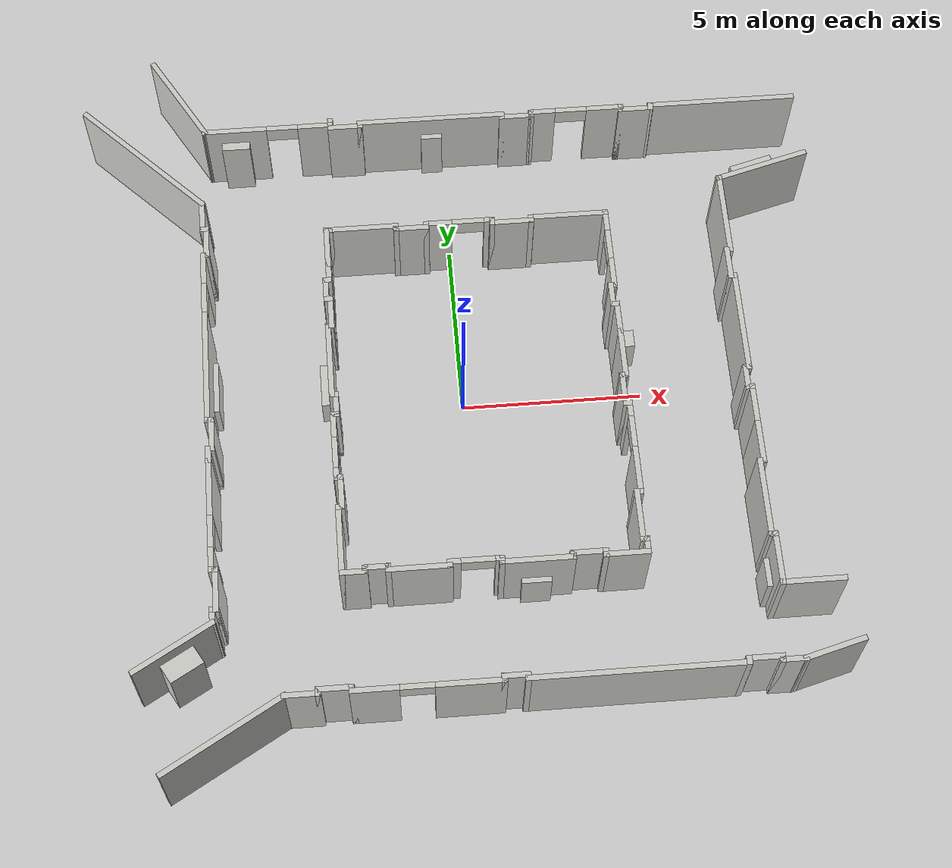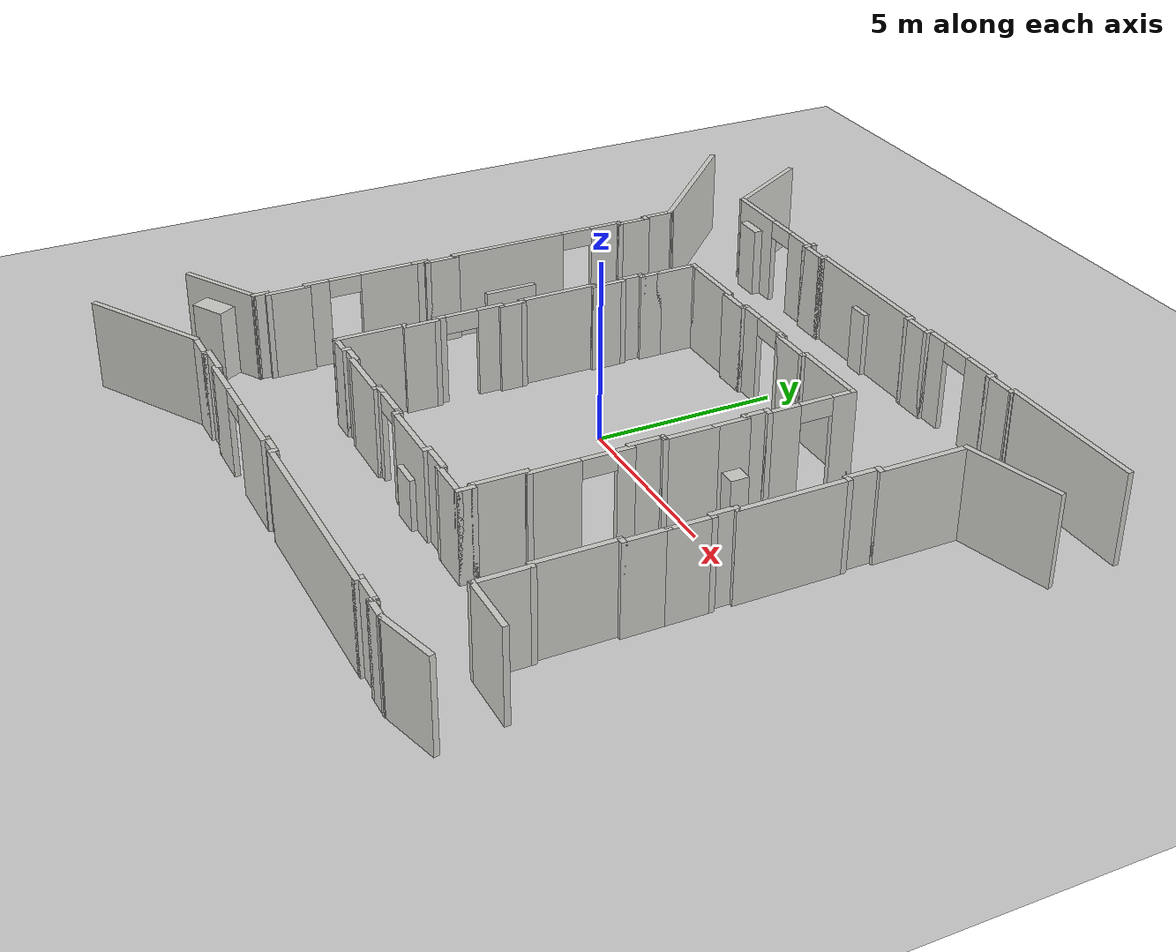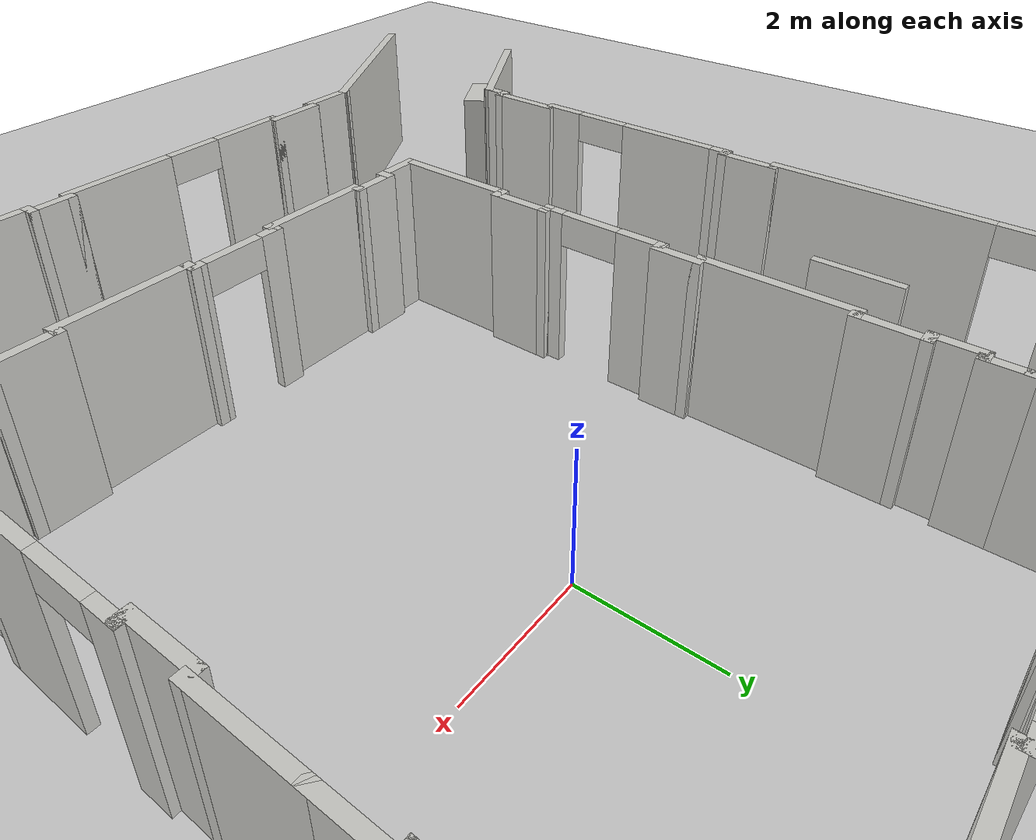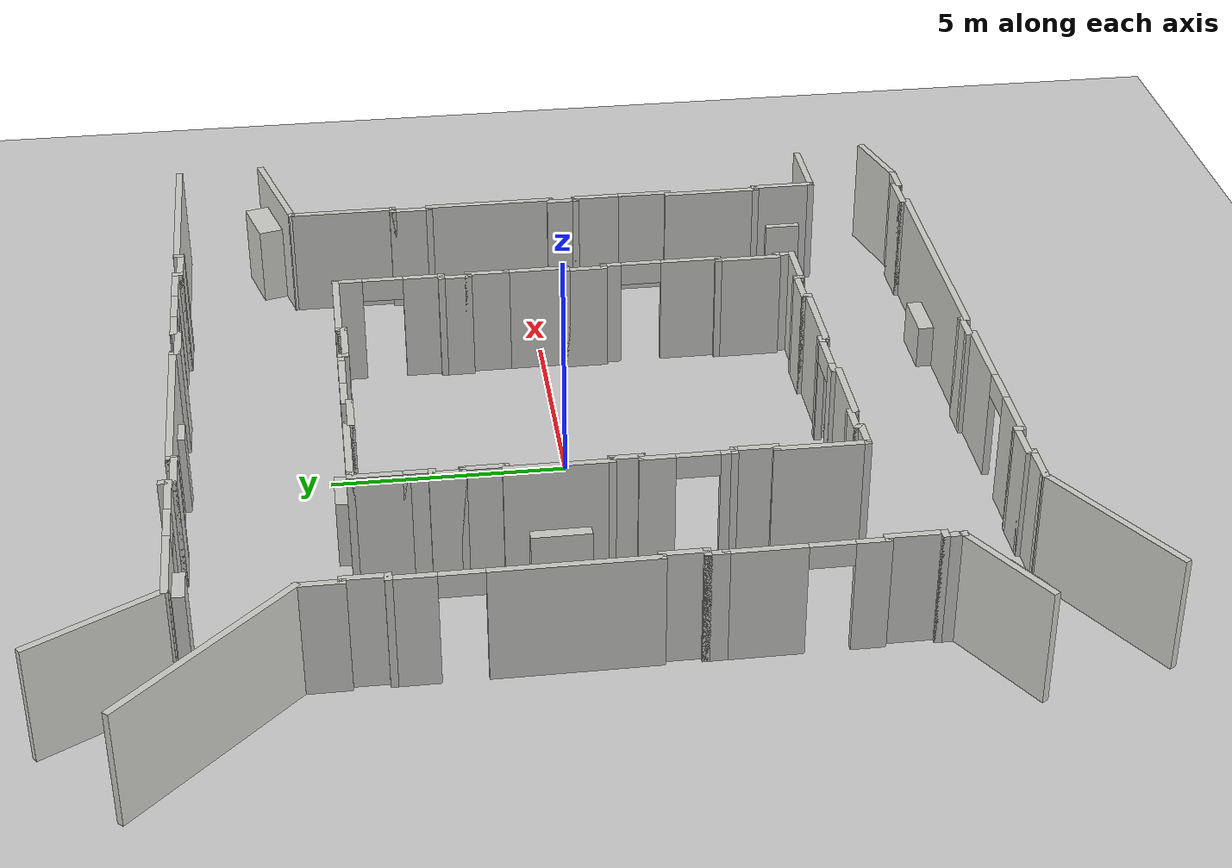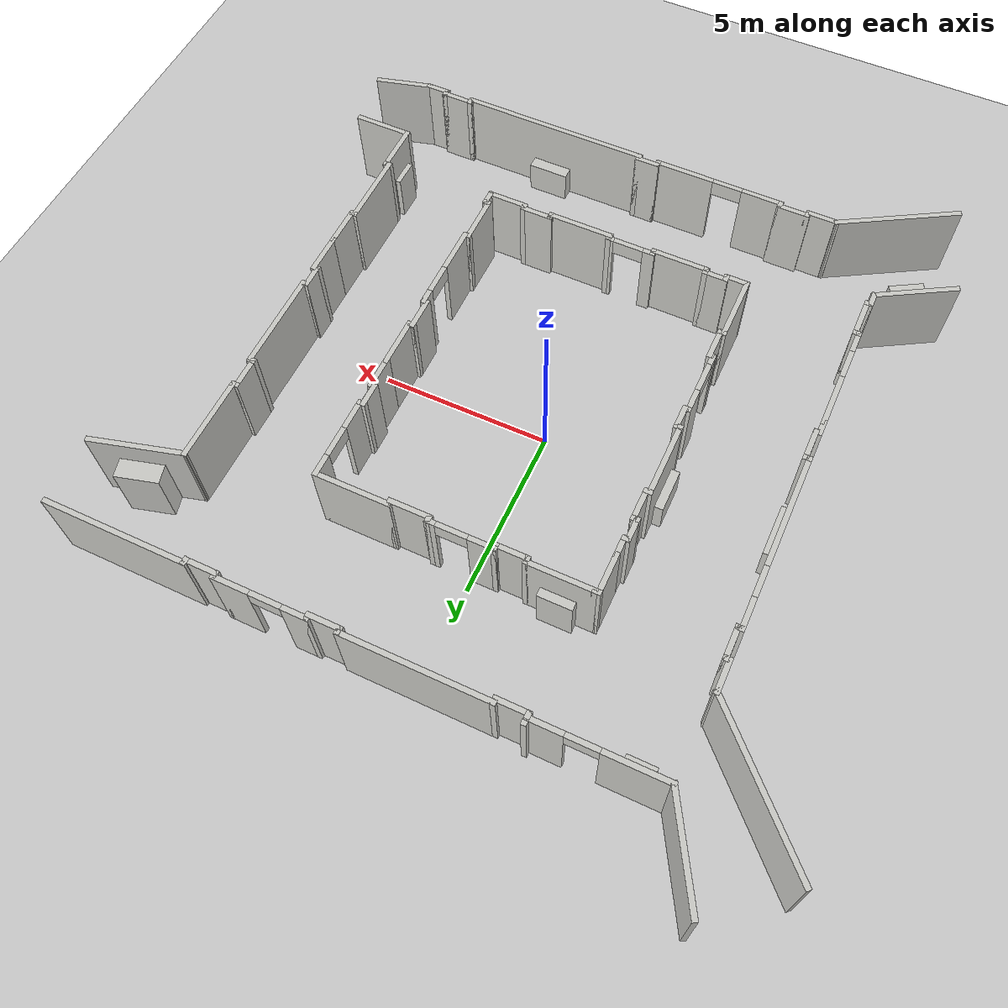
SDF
<sdf version="1.6">
 <world name="default">
  <light name="sun" type="directional">
   <pose>0 0 10 0 -0 0</pose>
   <diffuse>0.8 0.8 0.8 1</diffuse>
   <specular>0.1 0.1 0.1 1</specular>
   <attenuation>
    <range>1000</range>
    <constant>0.9</constant>
    <linear>0.01</linear>
    <quadratic>0.001</quadratic>
   </attenuation>
   <direction>-0.5 0.5 -1</direction>
  </light>
  <model name="ground_plane">
   <static>1</static>
   <link name="link">
    <collision name="collision">
     <geometry><plane><normal>0 0 1</normal><size>100 100</size></plane></geometry>
     <surface><friction><ode><mu>100</mu><mu2>50</mu2></ode></friction></surface>
    </collision>
    <visual name="visual">
     <cast_shadows>0</cast_shadows>
     <geometry><plane><normal>0 0 1</normal><size>100 100</size></plane></geometry>
     <material>
      <script><uri>file://media/materials/scripts/gazebo.material</uri><name>Gazebo/Grey</name></script>
     </material>
    </visual>
   </link>
  </model>
  <gravity>0 0 -9.8</gravity>
  <magnetic_field>6e-06 2.3e-05 -4.2e-05</magnetic_field>
  <atmosphere type="adiabatic"/>
  <physics name="default_physics" default="0" type="ode">
   <max_step_size>0.001</max_step_size>
   <real_time_factor>1</real_time_factor>
   <real_time_update_rate>1000</real_time_update_rate>
  </physics>
  <scene><ambient>0.4 0.4 0.4 1</ambient><background>0.7 0.7 0.7 1</background><shadows>1</shadows></scene>
  <spherical_coordinates>
   <surface_model>EARTH_WGS84</surface_model>
   <latitude_deg>0</latitude_deg>
   <longitude_deg>0</longitude_deg>
   <elevation>0</elevation>
   <heading_deg>0</heading_deg>
  </spherical_coordinates>
  <model name="mcbryde5">
   <pose>0.0004 -0.03414 0 0 -0 0</pose>
   <link name="Wall_102">
    <collision name="Wall_102_Collision">
     <geometry><box><size>0.15 0.15 2.5</size></box></geometry>
     <pose>0 0 1.25 0 -0 0</pose>
    </collision>
    <visual name="Wall_102_Visual">
     <pose>0 0 1.25 0 -0 0</pose>
     <geometry><box><size>0.15 0.15 2.5</size></box></geometry>
     <material>
      <script><uri>file://media/materials/scripts/gazebo.material</uri><name>Gazebo/CeilingTiled</name></script>
      <ambient>1 1 1 1</ambient>
     </material>
    </visual>
    <pose>-6.94903 4.93922 0 0 -0 0</pose>
   </link>
   <link name="Wall_103">
    <collision name="Wall_103_Collision">
     <geometry><box><size>0.25 0.15 2.5</size></box></geometry>
     <pose>0 0 1.25 0 -0 0</pose>
    </collision>
    <visual name="Wall_103_Visual">
     <pose>0 0 1.25 0 -0 0</pose>
     <geometry><box><size>0.25 0.15 2.5</size></box></geometry>
     <material>
      <script><uri>file://media/materials/scripts/gazebo.material</uri><name>Gazebo/CeilingTiled</name></script>
      <ambient>1 1 1 1</ambient>
     </material>
    </visual>
    <pose>-6.89903 4.93922 0 0 -0 0</pose>
   </link>
   <link name="Wall_104">
    <collision name="Wall_104_Collision">
     <geometry><box><size>1 0.15 2.5</size></box></geometry>
     <pose>0 0 1.25 0 -0 0</pose>
    </collision>
    <visual name="Wall_104_Visual">
     <pose>0 0 1.25 0 -0 0</pose>
     <geometry><box><size>1 0.15 2.5</size></box></geometry>
     <material>
      <script><uri>file://media/materials/scripts/gazebo.material</uri><name>Gazebo/CeilingTiled</name></script>
      <ambient>1 1 1 1</ambient>
     </material>
    </visual>
    <pose>-6.84903 4.51422 0 0 0 -1.5708</pose>
   </link>
   <link name="Wall_105">
    <collision name="Wall_105_Collision">
     <geometry><box><size>0.25 0.15 2.5</size></box></geometry>
     <pose>0 0 1.25 0 -0 0</pose>
    </collision>
    <visual name="Wall_105_Visual">
     <pose>0 0 1.25 0 -0 0</pose>
     <geometry><box><size>0.25 0.15 2.5</size></box></geometry>
     <material>
      <script><uri>file://media/materials/scripts/gazebo.material</uri><name>Gazebo/CeilingTiled</name></script>
      <ambient>1 1 1 1</ambient>
     </material>
    </visual>
    <pose>-6.89903 4.08922 0 0 -0 3.14159</pose>
   </link>
   <link name="Wall_106">
    <pose>-6.94903 1.53922 0 0 0 -1.5708</pose>
    <visual name="Wall_106_Visual_0">
     <pose>-2.13764 0 1.25 0 -0 0</pose>
     <geometry><box><size>0.974722 0.15 2.5</size></box></geometry>
     <material>
      <script><uri>file://media/materials/scripts/gazebo.material</uri><name>Gazebo/CeilingTiled</name></script>
      <ambient>1 1 1 1</ambient>
     </material>
    </visual>
    <collision name="Wall_106_Collision_0">
     <geometry><box><size>0.974722 0.15 2.5</size></box></geometry>
     <pose>-2.13764 0 1.25 0 -0 0</pose>
    </collision>
    <visual name="Wall_106_Visual_1">
     <pose>0.937361 0 1.25 0 -0 0</pose>
     <geometry><box><size>3.37528 0.15 2.5</size></box></geometry>
     <material>
      <script><uri>file://media/materials/scripts/gazebo.material</uri><name>Gazebo/CeilingTiled</name></script>
      <ambient>1 1 1 1</ambient>
     </material>
    </visual>
    <collision name="Wall_106_Collision_1">
     <geometry><box><size>3.37528 0.15 2.5</size></box></geometry>
     <pose>0.937361 0 1.25 0 -0 0</pose>
    </collision>
    <visual name="Wall_106_Visual_2">
     <pose>-1.20028 0 2.25 0 -0 0</pose>
     <geometry><box><size>0.9 0.15 0.5</size></box></geometry>
     <material>
      <script><uri>file://media/materials/scripts/gazebo.material</uri><name>Gazebo/CeilingTiled</name></script>
      <ambient>1 1 1 1</ambient>
     </material>
    </visual>
    <collision name="Wall_106_Collision_2">
     <geometry><box><size>0.9 0.15 0.5</size></box></geometry>
     <pose>-1.20028 0 2.25 0 -0 0</pose>
    </collision>
    <visual name="Wall_106_Visual_3">
     <pose>0.937361 0.15 0.6 0 -0 0</pose>
     <geometry><box><size>1.5 0.15 1.2</size></box></geometry>
     <material>
      <script><uri>file://media/materials/scripts/gazebo.material</uri><name>Gazebo/CeilingTiled</name></script>
      <ambient>0.6 0.6 1 1</ambient>
     </material>
    </visual>
    <collision name="Wall_106_Collision_3">
     <geometry><box><size>1.5 0.15 1.2</size></box></geometry>
     <pose>0.937361 0.15 0.6 0 -0 0</pose>
    </collision>
   </link>
   <link name="Wall_107">
    <collision name="Wall_107_Collision">
     <geometry><box><size>0.25 0.15 2.5</size></box></geometry>
     <pose>0 0 1.25 0 -0 0</pose>
    </collision>
    <visual name="Wall_107_Visual">
     <pose>0 0 1.25 0 -0 0</pose>
     <geometry><box><size>0.25 0.15 2.5</size></box></geometry>
     <material>
      <script><uri>file://media/materials/scripts/gazebo.material</uri><name>Gazebo/CeilingTiled</name></script>
      <ambient>1 1 1 1</ambient>
     </material>
    </visual>
    <pose>-6.89903 -1.01078 0 0 -0 0</pose>
   </link>
   <link name="Wall_108">
    <collision name="Wall_108_Collision">
     <geometry><box><size>1 0.15 2.5</size></box></geometry>
     <pose>0 0 1.25 0 -0 0</pose>
    </collision>
    <visual name="Wall_108_Visual">
     <pose>0 0 1.25 0 -0 0</pose>
     <geometry><box><size>1 0.15 2.5</size></box></geometry>
     <material>
      <script><uri>file://media/materials/scripts/gazebo.material</uri><name>Gazebo/CeilingTiled</name></script>
      <ambient>1 1 1 1</ambient>
     </material>
    </visual>
    <pose>-6.84903 -1.43578 0 0 0 -1.5708</pose>
   </link>
   <link name="Wall_109">
    <collision name="Wall_109_Collision">
     <geometry><box><size>0.25 0.15 2.5</size></box></geometry>
     <pose>0 0 1.25 0 -0 0</pose>
    </collision>
    <visual name="Wall_109_Visual">
     <pose>0 0 1.25 0 -0 0</pose>
     <geometry><box><size>0.25 0.15 2.5</size></box></geometry>
     <material>
      <script><uri>file://media/materials/scripts/gazebo.material</uri><name>Gazebo/CeilingTiled</name></script>
      <ambient>1 1 1 1</ambient>
     </material>
    </visual>
    <pose>-6.89903 -1.86078 0 0 -0 3.14159</pose>
   </link>
   <link name="Wall_110">
    <collision name="Wall_110_Collision">
     <geometry><box><size>0.5 0.15 2.5</size></box></geometry>
     <pose>0 0 1.25 0 -0 0</pose>
    </collision>
    <visual name="Wall_110_Visual">
     <pose>0 0 1.25 0 -0 0</pose>
     <geometry><box><size>0.5 0.15 2.5</size></box></geometry>
     <material>
      <script><uri>file://media/materials/scripts/gazebo.material</uri><name>Gazebo/CeilingTiled</name></script>
      <ambient>1 1 1 1</ambient>
     </material>
    </visual>
    <pose>-6.94903 -2.03578 0 0 0 -1.5708</pose>
   </link>
   <link name="Wall_112">
    <pose>-6.94903 -3.76078 0 0 0 -1.5708</pose>
    <visual name="Wall_112_Visual_0">
     <pose>-0.803013 0 1.25 0 -0 0</pose>
     <geometry><box><size>1.64397 0.15 2.5</size></box></geometry>
     <material>
      <script><uri>file://media/materials/scripts/gazebo.material</uri><name>Gazebo/CeilingTiled</name></script>
      <ambient>1 1 1 1</ambient>
     </material>
    </visual>
    <collision name="Wall_112_Collision_0">
     <geometry><box><size>1.64397 0.15 2.5</size></box></geometry>
     <pose>-0.803013 0 1.25 0 -0 0</pose>
    </collision>
    <visual name="Wall_112_Visual_1">
     <pose>1.27199 0 1.25 0 -0 0</pose>
     <geometry><box><size>0.706025 0.15 2.5</size></box></geometry>
     <material>
      <script><uri>file://media/materials/scripts/gazebo.material</uri><name>Gazebo/CeilingTiled</name></script>
      <ambient>1 1 1 1</ambient>
     </material>
    </visual>
    <collision name="Wall_112_Collision_1">
     <geometry><box><size>0.706025 0.15 2.5</size></box></geometry>
     <pose>1.27199 0 1.25 0 -0 0</pose>
    </collision>
    <visual name="Wall_112_Visual_2">
     <pose>0.468975 0 2.25 0 -0 0</pose>
     <geometry><box><size>0.9 0.15 0.5</size></box></geometry>
     <material>
      <script><uri>file://media/materials/scripts/gazebo.material</uri><name>Gazebo/CeilingTiled</name></script>
      <ambient>1 1 1 1</ambient>
     </material>
    </visual>
    <collision name="Wall_112_Collision_2">
     <geometry><box><size>0.9 0.15 0.5</size></box></geometry>
     <pose>0.468975 0 2.25 0 -0 0</pose>
    </collision>
   </link>
   <link name="Wall_113">
    <collision name="Wall_113_Collision">
     <geometry><box><size>0.25 0.15 2.5</size></box></geometry>
     <pose>0 0 1.25 0 -0 0</pose>
    </collision>
    <visual name="Wall_113_Visual">
     <pose>0 0 1.25 0 -0 0</pose>
     <geometry><box><size>0.25 0.15 2.5</size></box></geometry>
     <material>
      <script><uri>file://media/materials/scripts/gazebo.material</uri><name>Gazebo/CeilingTiled</name></script>
      <ambient>1 1 1 1</ambient>
     </material>
    </visual>
    <pose>-6.89903 -5.31078 0 0 -0 0</pose>
   </link>
   <link name="Wall_114">
    <collision name="Wall_114_Collision">
     <geometry><box><size>1.25 0.15 2.5</size></box></geometry>
     <pose>0 0 1.25 0 -0 0</pose>
    </collision>
    <visual name="Wall_114_Visual">
     <pose>0 0 1.25 0 -0 0</pose>
     <geometry><box><size>1.25 0.15 2.5</size></box></geometry>
     <material>
      <script><uri>file://media/materials/scripts/gazebo.material</uri><name>Gazebo/CeilingTiled</name></script>
      <ambient>1 1 1 1</ambient>
     </material>
    </visual>
    <pose>-6.84903 -5.86078 0 0 0 -1.5708</pose>
   </link>
   <link name="Wall_115">
    <collision name="Wall_115_Collision">
     <geometry><box><size>0.25 0.15 2.5</size></box></geometry>
     <pose>0 0 1.25 0 -0 0</pose>
    </collision>
    <visual name="Wall_115_Visual">
     <pose>0 0 1.25 0 -0 0</pose>
     <geometry><box><size>0.25 0.15 2.5</size></box></geometry>
     <material>
      <script><uri>file://media/materials/scripts/gazebo.material</uri><name>Gazebo/CeilingTiled</name></script>
      <ambient>1 1 1 1</ambient>
     </material>
    </visual>
    <pose>-6.89903 -6.41078 0 0 -0 3.14159</pose>
   </link>
   <link name="Wall_116">
    <collision name="Wall_116_Collision">
     <geometry><box><size>0.5 0.15 2.5</size></box></geometry>
     <pose>0 0 1.25 0 -0 0</pose>
    </collision>
    <visual name="Wall_116_Visual">
     <pose>0 0 1.25 0 -0 0</pose>
     <geometry><box><size>0.5 0.15 2.5</size></box></geometry>
     <material>
      <script><uri>file://media/materials/scripts/gazebo.material</uri><name>Gazebo/CeilingTiled</name></script>
      <ambient>1 1 1 1</ambient>
     </material>
    </visual>
    <pose>-6.94903 -6.58578 0 0 0 -1.5708</pose>
   </link>
   <link name="Wall_117">
    <collision name="Wall_117_Collision_0">
     <geometry><box><size>2.5 0.15 2.5</size></box></geometry>
     <pose>0 0 1.25 0 -0 0</pose>
    </collision>
    <visual name="Wall_117_Visual_0">
     <pose>0 0 1.25 0 -0 0</pose>
     <geometry><box><size>2.5 0.15 2.5</size></box></geometry>
     <material>
      <script><uri>file://media/materials/scripts/gazebo.material</uri><name>Gazebo/CeilingTiled</name></script>
      <ambient>1 1 1 1</ambient>
     </material>
    </visual>
    <collision name="Wall_117_Collision_1">
     <geometry><box><size>1 0.55 2</size></box></geometry>
     <pose>0 0.35 1 0 -0 0</pose>
    </collision>
    <visual name="Wall_117_Visual_1">
     <pose>0 0.35 1 0 -0 0</pose>
     <geometry><box><size>1 0.55 2</size></box></geometry>
     <material>
      <script><uri>file://media/materials/scripts/gazebo.material</uri><name>Gazebo/CeilingTiled</name></script>
      <ambient>0.3 1 0.3 1</ambient>
     </material>
    </visual>
    <pose>-7.96661 -7.34828 0 0 0 -2.61799</pose>
   </link>
   <link name="Wall_119">
    <collision name="Wall_119_Collision">
     <geometry><box><size>3.75 0.15 2.5</size></box></geometry>
     <pose>0 0 1.25 0 -0 0</pose>
    </collision>
    <visual name="Wall_119_Visual">
     <pose>0 0 1.25 0 -0 0</pose>
     <geometry><box><size>3.75 0.15 2.5</size></box></geometry>
     <material>
      <script><uri>file://media/materials/scripts/gazebo.material</uri><name>Gazebo/CeilingTiled</name></script>
      <ambient>1 1 1 1</ambient>
     </material>
    </visual>
    <pose>-6.76357 -9.73795 0 0 -0 0.523599</pose>
   </link>
   <link name="Wall_120">
    <collision name="Wall_120_Collision">
     <geometry><box><size>1 0.15 2.5</size></box></geometry>
     <pose>0 0 1.25 0 -0 0</pose>
    </collision>
    <visual name="Wall_120_Visual">
     <pose>0 0 1.25 0 -0 0</pose>
     <geometry><box><size>1 0.15 2.5</size></box></geometry>
     <material>
      <script><uri>file://media/materials/scripts/gazebo.material</uri><name>Gazebo/CeilingTiled</name></script>
      <ambient>1 1 1 1</ambient>
     </material>
    </visual>
    <pose>-4.77972 -8.83795 0 0 -0 0</pose>
   </link>
   <link name="Wall_121">
    <collision name="Wall_121_Collision">
     <geometry><box><size>0.25 0.15 2.5</size></box></geometry>
     <pose>0 0 1.25 0 -0 0</pose>
    </collision>
    <visual name="Wall_121_Visual">
     <pose>0 0 1.25 0 -0 0</pose>
     <geometry><box><size>0.25 0.15 2.5</size></box></geometry>
     <material>
      <script><uri>file://media/materials/scripts/gazebo.material</uri><name>Gazebo/CeilingTiled</name></script>
      <ambient>1 1 1 1</ambient>
     </material>
    </visual>
    <pose>-4.35472 -8.78795 0 0 -0 1.5708</pose>
   </link>
   <link name="Wall_122">
    <collision name="Wall_122_Collision">
     <geometry><box><size>1 0.15 2.5</size></box></geometry>
     <pose>0 0 1.25 0 -0 0</pose>
    </collision>
    <visual name="Wall_122_Visual">
     <pose>0 0 1.25 0 -0 0</pose>
     <geometry><box><size>1 0.15 2.5</size></box></geometry>
     <material>
      <script><uri>file://media/materials/scripts/gazebo.material</uri><name>Gazebo/CeilingTiled</name></script>
      <ambient>1 1 1 1</ambient>
     </material>
    </visual>
    <pose>-3.92972 -8.73795 0 0 -0 0</pose>
   </link>
   <link name="Wall_123">
    <collision name="Wall_123_Collision">
     <geometry><box><size>0.25 0.15 2.5</size></box></geometry>
     <pose>0 0 1.25 0 -0 0</pose>
    </collision>
    <visual name="Wall_123_Visual">
     <pose>0 0 1.25 0 -0 0</pose>
     <geometry><box><size>0.25 0.15 2.5</size></box></geometry>
     <material>
      <script><uri>file://media/materials/scripts/gazebo.material</uri><name>Gazebo/CeilingTiled</name></script>
      <ambient>1 1 1 1</ambient>
     </material>
    </visual>
    <pose>-3.50472 -8.78795 0 0 0 -1.5708</pose>
   </link>
   <link name="Wall_124">
    <pose>-1.57972 -8.83795 0 0 -0 0</pose>
    <visual name="Wall_124_Visual_0">
     <pose>-1.36383 0 1.25 0 -0 0</pose>
     <geometry><box><size>1.27234 0.15 2.5</size></box></geometry>
     <material>
      <script><uri>file://media/materials/scripts/gazebo.material</uri><name>Gazebo/CeilingTiled</name></script>
      <ambient>1 1 1 1</ambient>
     </material>
    </visual>
    <collision name="Wall_124_Collision_0">
     <geometry><box><size>1.27234 0.15 2.5</size></box></geometry>
     <pose>-1.36383 0 1.25 0 -0 0</pose>
    </collision>
    <visual name="Wall_124_Visual_1">
     <pose>1.08617 0 1.25 0 -0 0</pose>
     <geometry><box><size>1.82766 0.15 2.5</size></box></geometry>
     <material>
      <script><uri>file://media/materials/scripts/gazebo.material</uri><name>Gazebo/CeilingTiled</name></script>
      <ambient>1 1 1 1</ambient>
     </material>
    </visual>
    <collision name="Wall_124_Collision_1">
     <geometry><box><size>1.82766 0.15 2.5</size></box></geometry>
     <pose>1.08617 0 1.25 0 -0 0</pose>
    </collision>
    <visual name="Wall_124_Visual_2">
     <pose>-0.277656 0 2.25 0 -0 0</pose>
     <geometry><box><size>0.9 0.15 0.5</size></box></geometry>
     <material>
      <script><uri>file://media/materials/scripts/gazebo.material</uri><name>Gazebo/CeilingTiled</name></script>
      <ambient>1 1 1 1</ambient>
     </material>
    </visual>
    <collision name="Wall_124_Collision_2">
     <geometry><box><size>0.9 0.15 0.5</size></box></geometry>
     <pose>-0.277656 0 2.25 0 -0 0</pose>
    </collision>
   </link>
   <link name="Wall_125">
    <collision name="Wall_125_Collision">
     <geometry><box><size>0.25 0.15 2.5</size></box></geometry>
     <pose>0 0 1.25 0 -0 0</pose>
    </collision>
    <visual name="Wall_125_Visual">
     <pose>0 0 1.25 0 -0 0</pose>
     <geometry><box><size>0.25 0.15 2.5</size></box></geometry>
     <material>
      <script><uri>file://media/materials/scripts/gazebo.material</uri><name>Gazebo/CeilingTiled</name></script>
      <ambient>1 1 1 1</ambient>
     </material>
    </visual>
    <pose>0.345276 -8.78795 0 0 -0 1.5708</pose>
   </link>
   <link name="Wall_126">
    <collision name="Wall_126_Collision">
     <geometry><box><size>0.75 0.15 2.5</size></box></geometry>
     <pose>0 0 1.25 0 -0 0</pose>
    </collision>
    <visual name="Wall_126_Visual">
     <pose>0 0 1.25 0 -0 0</pose>
     <geometry><box><size>0.75 0.15 2.5</size></box></geometry>
     <material>
      <script><uri>file://media/materials/scripts/gazebo.material</uri><name>Gazebo/CeilingTiled</name></script>
      <ambient>1 1 1 1</ambient>
     </material>
    </visual>
    <pose>0.645276 -8.73795 0 0 -0 0</pose>
   </link>
   <link name="Wall_127">
    <collision name="Wall_127_Collision">
     <geometry><box><size>0.25 0.15 2.5</size></box></geometry>
     <pose>0 0 1.25 0 -0 0</pose>
    </collision>
    <visual name="Wall_127_Visual">
     <pose>0 0 1.25 0 -0 0</pose>
     <geometry><box><size>0.25 0.15 2.5</size></box></geometry>
     <material>
      <script><uri>file://media/materials/scripts/gazebo.material</uri><name>Gazebo/CeilingTiled</name></script>
      <ambient>1 1 1 1</ambient>
     </material>
    </visual>
    <pose>0.945276 -8.78795 0 0 0 -1.5708</pose>
   </link>
   <link name="Wall_128">
    <collision name="Wall_128_Collision_0">
     <geometry><box><size>5.75 0.15 2.5</size></box></geometry>
     <pose>0 0 1.25 0 -0 0</pose>
    </collision>
    <visual name="Wall_128_Visual_0">
     <pose>0 0 1.25 0 -0 0</pose>
     <geometry><box><size>5.75 0.15 2.5</size></box></geometry>
     <material>
      <script><uri>file://media/materials/scripts/gazebo.material</uri><name>Gazebo/CeilingTiled</name></script>
      <ambient>1 1 1 1</ambient>
     </material>
    </visual>
    <collision name="Wall_128_Collision_1">
     <geometry><box><size>1.2 0.35 1</size></box></geometry>
     <pose>0 0.25 0.5 0 -0 0</pose>
    </collision>
    <visual name="Wall_128_Visual_1">
     <pose>0 0.25 0.5 0 -0 0</pose>
     <geometry><box><size>1.2 0.35 1</size></box></geometry>
     <material>
      <script><uri>file://media/materials/scripts/gazebo.material</uri><name>Gazebo/CeilingTiled</name></script>
      <ambient>0.4 0.4 1 1</ambient>
     </material>
    </visual>
    <pose>3.74528 -8.83795 0 0 -0 0</pose>
   </link>
   <link name="Wall_129">
    <collision name="Wall_129_Collision">
     <geometry><box><size>0.25 0.15 2.5</size></box></geometry>
     <pose>0 0 1.25 0 -0 0</pose>
    </collision>
    <visual name="Wall_129_Visual">
     <pose>0 0 1.25 0 -0 0</pose>
     <geometry><box><size>0.25 0.15 2.5</size></box></geometry>
     <material>
      <script><uri>file://media/materials/scripts/gazebo.material</uri><name>Gazebo/CeilingTiled</name></script>
      <ambient>1 1 1 1</ambient>
     </material>
    </visual>
    <pose>6.54528 -8.78795 0 0 -0 1.5708</pose>
   </link>
   <link name="Wall_130">
    <collision name="Wall_130_Collision">
     <geometry><box><size>1 0.15 2.5</size></box></geometry>
     <pose>0 0 1.25 0 -0 0</pose>
    </collision>
    <visual name="Wall_130_Visual">
     <pose>0 0 1.25 0 -0 0</pose>
     <geometry><box><size>1 0.15 2.5</size></box></geometry>
     <material>
      <script><uri>file://media/materials/scripts/gazebo.material</uri><name>Gazebo/CeilingTiled</name></script>
      <ambient>1 1 1 1</ambient>
     </material>
    </visual>
    <pose>6.97028 -8.73795 0 0 -0 0</pose>
   </link>
   <link name="Wall_131">
    <collision name="Wall_131_Collision">
     <geometry><box><size>0.25 0.15 2.5</size></box></geometry>
     <pose>0 0 1.25 0 -0 0</pose>
    </collision>
    <visual name="Wall_131_Visual">
     <pose>0 0 1.25 0 -0 0</pose>
     <geometry><box><size>0.25 0.15 2.5</size></box></geometry>
     <material>
      <script><uri>file://media/materials/scripts/gazebo.material</uri><name>Gazebo/CeilingTiled</name></script>
      <ambient>1 1 1 1</ambient>
     </material>
    </visual>
    <pose>7.39528 -8.78795 0 0 0 -1.5708</pose>
   </link>
   <link name="Wall_132">
    <collision name="Wall_132_Collision">
     <geometry><box><size>0.75 0.15 2.5</size></box></geometry>
     <pose>0 0 1.25 0 -0 0</pose>
    </collision>
    <visual name="Wall_132_Visual">
     <pose>0 0 1.25 0 -0 0</pose>
     <geometry><box><size>0.75 0.15 2.5</size></box></geometry>
     <material>
      <script><uri>file://media/materials/scripts/gazebo.material</uri><name>Gazebo/CeilingTiled</name></script>
      <ambient>1 1 1 1</ambient>
     </material>
    </visual>
    <pose>7.69528 -8.83795 0 0 -0 0</pose>
   </link>
   <link name="Wall_133">
    <collision name="Wall_133_Collision">
     <geometry><box><size>1.75 0.15 2.5</size></box></geometry>
     <pose>0 0 1.25 0 -0 0</pose>
    </collision>
    <visual name="Wall_133_Visual">
     <pose>0 0 1.25 0 -0 0</pose>
     <geometry><box><size>1.75 0.15 2.5</size></box></geometry>
     <material>
      <script><uri>file://media/materials/scripts/gazebo.material</uri><name>Gazebo/CeilingTiled</name></script>
      <ambient>1 1 1 1</ambient>
     </material>
    </visual>
    <pose>8.76802 -8.6309 0 0 -0 0.261799</pose>
   </link>
   <link name="Wall_136">
    <collision name="Wall_136_Collision">
     <geometry><box><size>1.75 0.15 2.5</size></box></geometry>
     <pose>0 0 1.25 0 -0 0</pose>
    </collision>
    <visual name="Wall_136_Visual">
     <pose>0 0 1.25 0 -0 0</pose>
     <geometry><box><size>1.75 0.15 2.5</size></box></geometry>
     <material>
      <script><uri>file://media/materials/scripts/gazebo.material</uri><name>Gazebo/CeilingTiled</name></script>
      <ambient>1 1 1 1</ambient>
     </material>
    </visual>
    <pose>8.50453 -6.75972 0 0 -0 3.14159</pose>
   </link>
   <link name="Wall_137">
    <collision name="Wall_137_Collision_0">
     <geometry><box><size>1.5 0.15 2.5</size></box></geometry>
     <pose>0 0 1.25 0 -0 0</pose>
    </collision>
    <visual name="Wall_137_Visual_0">
     <pose>0 0 1.25 0 -0 0</pose>
     <geometry><box><size>1.5 0.15 2.5</size></box></geometry>
     <material>
      <script><uri>file://media/materials/scripts/gazebo.material</uri><name>Gazebo/CeilingTiled</name></script>
      <ambient>1 1 1 1</ambient>
     </material>
    </visual>
    <collision name="Wall_137_Collision_1">
     <geometry><box><size>0.8 0.15 1.5</size></box></geometry>
     <pose>0 0.15 0.75 0 -0 0</pose>
    </collision>
    <visual name="Wall_137_Visual_1">
     <pose>0 0.15 0.75 0 -0 0</pose>
     <geometry><box><size>0.8 0.15 1.5</size></box></geometry>
     <material>
      <script><uri>file://media/materials/scripts/gazebo.material</uri><name>Gazebo/CeilingTiled</name></script>
      <ambient>1 0.6 1 1</ambient>
     </material>
    </visual>
    <pose>7.70453 -6.08472 0 0 -0 1.5708</pose>
   </link>
   <link name="Wall_138">
    <collision name="Wall_138_Collision">
     <geometry><box><size>0.25 0.15 2.5</size></box></geometry>
     <pose>0 0 1.25 0 -0 0</pose>
    </collision>
    <visual name="Wall_138_Visual">
     <pose>0 0 1.25 0 -0 0</pose>
     <geometry><box><size>0.25 0.15 2.5</size></box></geometry>
     <material>
      <script><uri>file://media/materials/scripts/gazebo.material</uri><name>Gazebo/CeilingTiled</name></script>
      <ambient>1 1 1 1</ambient>
     </material>
    </visual>
    <pose>7.65453 -5.40972 0 0 -0 3.14159</pose>
   </link>
   <link name="Wall_139">
    <collision name="Wall_139_Collision">
     <geometry><box><size>2.25 0.15 2.5</size></box></geometry>
     <pose>0 0 1.25 0 -0 0</pose>
    </collision>
    <visual name="Wall_139_Visual">
     <pose>0 0 1.25 0 -0 0</pose>
     <geometry><box><size>2.25 0.15 2.5</size></box></geometry>
     <material>
      <script><uri>file://media/materials/scripts/gazebo.material</uri><name>Gazebo/CeilingTiled</name></script>
      <ambient>1 1 1 1</ambient>
     </material>
    </visual>
    <pose>7.60453 -4.35972 0 0 -0 1.5708</pose>
   </link>
   <link name="Wall_14">
    <collision name="Wall_14_Collision">
     <geometry><box><size>0.15 0.15 2.5</size></box></geometry>
     <pose>0 0 1.25 0 -0 0</pose>
    </collision>
    <visual name="Wall_14_Visual">
     <pose>0 0 1.25 0 -0 0</pose>
     <geometry><box><size>0.15 0.15 2.5</size></box></geometry>
     <material>
      <script><uri>file://media/materials/scripts/gazebo.material</uri><name>Gazebo/CeilingTiled</name></script>
      <ambient>1 1 1 1</ambient>
     </material>
    </visual>
    <pose>-3.20531 8.30498 0 0 -0 0</pose>
   </link>
   <link name="Wall_140">
    <collision name="Wall_140_Collision">
     <geometry><box><size>0.25 0.15 2.5</size></box></geometry>
     <pose>0 0 1.25 0 -0 0</pose>
    </collision>
    <visual name="Wall_140_Visual">
     <pose>0 0 1.25 0 -0 0</pose>
     <geometry><box><size>0.25 0.15 2.5</size></box></geometry>
     <material>
      <script><uri>file://media/materials/scripts/gazebo.material</uri><name>Gazebo/CeilingTiled</name></script>
      <ambient>1 1 1 1</ambient>
     </material>
    </visual>
    <pose>7.65453 -3.30972 0 0 -0 0</pose>
   </link>
   <link name="Wall_141">
    <collision name="Wall_141_Collision">
     <geometry><box><size>1.25 0.15 2.5</size></box></geometry>
     <pose>0 0 1.25 0 -0 0</pose>
    </collision>
    <visual name="Wall_141_Visual">
     <pose>0 0 1.25 0 -0 0</pose>
     <geometry><box><size>1.25 0.15 2.5</size></box></geometry>
     <material>
      <script><uri>file://media/materials/scripts/gazebo.material</uri><name>Gazebo/CeilingTiled</name></script>
      <ambient>1 1 1 1</ambient>
     </material>
    </visual>
    <pose>7.70453 -2.75972 0 0 -0 1.5708</pose>
   </link>
   <link name="Wall_143">
    <collision name="Wall_143_Collision">
     <geometry><box><size>1.25 0.15 2.5</size></box></geometry>
     <pose>0 0 1.25 0 -0 0</pose>
    </collision>
    <visual name="Wall_143_Visual">
     <pose>0 0 1.25 0 -0 0</pose>
     <geometry><box><size>1.25 0.15 2.5</size></box></geometry>
     <material>
      <script><uri>file://media/materials/scripts/gazebo.material</uri><name>Gazebo/CeilingTiled</name></script>
      <ambient>1 1 1 1</ambient>
     </material>
    </visual>
    <pose>7.70453 -1.65972 0 0 -0 1.5708</pose>
   </link>
   <link name="Wall_144">
    <collision name="Wall_144_Collision">
     <geometry><box><size>0.25 0.15 2.5</size></box></geometry>
     <pose>0 0 1.25 0 -0 0</pose>
    </collision>
    <visual name="Wall_144_Visual">
     <pose>0 0 1.25 0 -0 0</pose>
     <geometry><box><size>0.25 0.15 2.5</size></box></geometry>
     <material>
      <script><uri>file://media/materials/scripts/gazebo.material</uri><name>Gazebo/CeilingTiled</name></script>
      <ambient>1 1 1 1</ambient>
     </material>
    </visual>
    <pose>7.65453 -1.10972 0 0 -0 3.14159</pose>
   </link>
   <link name="Wall_145">
    <collision name="Wall_145_Collision">
     <geometry><box><size>0.75 0.15 2.5</size></box></geometry>
     <pose>0 0 1.25 0 -0 0</pose>
    </collision>
    <visual name="Wall_145_Visual">
     <pose>0 0 1.25 0 -0 0</pose>
     <geometry><box><size>0.75 0.15 2.5</size></box></geometry>
     <material>
      <script><uri>file://media/materials/scripts/gazebo.material</uri><name>Gazebo/CeilingTiled</name></script>
      <ambient>1 1 1 1</ambient>
     </material>
    </visual>
    <pose>7.60453 -0.809722 0 0 -0 1.5708</pose>
   </link>
   <link name="Wall_146">
    <collision name="Wall_146_Collision">
     <geometry><box><size>0.25 0.15 2.5</size></box></geometry>
     <pose>0 0 1.25 0 -0 0</pose>
    </collision>
    <visual name="Wall_146_Visual">
     <pose>0 0 1.25 0 -0 0</pose>
     <geometry><box><size>0.25 0.15 2.5</size></box></geometry>
     <material>
      <script><uri>file://media/materials/scripts/gazebo.material</uri><name>Gazebo/CeilingTiled</name></script>
      <ambient>1 1 1 1</ambient>
     </material>
    </visual>
    <pose>7.65453 -0.509722 0 0 -0 0</pose>
   </link>
   <link name="Wall_147">
    <collision name="Wall_147_Collision">
     <geometry><box><size>3 0.15 2.5</size></box></geometry>
     <pose>0 0 1.25 0 -0 0</pose>
    </collision>
    <visual name="Wall_147_Visual">
     <pose>0 0 1.25 0 -0 0</pose>
     <geometry><box><size>3 0.15 2.5</size></box></geometry>
     <material>
      <script><uri>file://media/materials/scripts/gazebo.material</uri><name>Gazebo/CeilingTiled</name></script>
      <ambient>1 1 1 1</ambient>
     </material>
    </visual>
    <pose>7.70453 0.915278 0 0 -0 1.5708</pose>
   </link>
   <link name="Wall_149">
    <collision name="Wall_149_Collision">
     <geometry><box><size>0.25 0.15 2.5</size></box></geometry>
     <pose>0 0 1.25 0 -0 0</pose>
    </collision>
    <visual name="Wall_149_Visual">
     <pose>0 0 1.25 0 -0 0</pose>
     <geometry><box><size>0.25 0.15 2.5</size></box></geometry>
     <material>
      <script><uri>file://media/materials/scripts/gazebo.material</uri><name>Gazebo/CeilingTiled</name></script>
      <ambient>1 1 1 1</ambient>
     </material>
    </visual>
    <pose>7.65453 2.34028 0 0 -0 3.14159</pose>
   </link>
   <link name="Wall_150">
    <collision name="Wall_150_Collision">
     <geometry><box><size>1 0.15 2.5</size></box></geometry>
     <pose>0 0 1.25 0 -0 0</pose>
    </collision>
    <visual name="Wall_150_Visual">
     <pose>0 0 1.25 0 -0 0</pose>
     <geometry><box><size>1 0.15 2.5</size></box></geometry>
     <material>
      <script><uri>file://media/materials/scripts/gazebo.material</uri><name>Gazebo/CeilingTiled</name></script>
      <ambient>1 1 1 1</ambient>
     </material>
    </visual>
    <pose>7.60453 2.76528 0 0 -0 1.5708</pose>
   </link>
   <link name="Wall_151">
    <collision name="Wall_151_Collision">
     <geometry><box><size>0.25 0.15 2.5</size></box></geometry>
     <pose>0 0 1.25 0 -0 0</pose>
    </collision>
    <visual name="Wall_151_Visual">
     <pose>0 0 1.25 0 -0 0</pose>
     <geometry><box><size>0.25 0.15 2.5</size></box></geometry>
     <material>
      <script><uri>file://media/materials/scripts/gazebo.material</uri><name>Gazebo/CeilingTiled</name></script>
      <ambient>1 1 1 1</ambient>
     </material>
    </visual>
    <pose>7.65453 3.19028 0 0 -0 0</pose>
   </link>
   <link name="Wall_152">
    <collision name="Wall_152_Collision">
     <geometry><box><size>2.5 0.15 2.5</size></box></geometry>
     <pose>0 0 1.25 0 -0 0</pose>
    </collision>
    <visual name="Wall_152_Visual">
     <pose>0 0 1.25 0 -0 0</pose>
     <geometry><box><size>2.5 0.15 2.5</size></box></geometry>
     <material>
      <script><uri>file://media/materials/scripts/gazebo.material</uri><name>Gazebo/CeilingTiled</name></script>
      <ambient>1 1 1 1</ambient>
     </material>
    </visual>
    <pose>7.70453 4.36528 0 0 -0 1.5708</pose>
   </link>
   <link name="Wall_153">
    <collision name="Wall_153_Collision_0">
     <geometry><box><size>2.75 0.15 2.5</size></box></geometry>
     <pose>0 0 1.25 0 -0 0</pose>
    </collision>
    <visual name="Wall_153_Visual_0">
     <pose>0 0 1.25 0 -0 0</pose>
     <geometry><box><size>2.75 0.15 2.5</size></box></geometry>
     <material>
      <script><uri>file://media/materials/scripts/gazebo.material</uri><name>Gazebo/CeilingTiled</name></script>
      <ambient>1 1 1 1</ambient>
     </material>
    </visual>
    <collision name="Wall_153_Collision_1">
     <geometry><box><size>1.25 0.55 1.8</size></box></geometry>
     <pose>0 0.35 0.9 0 -0 0</pose>
    </collision>
    <visual name="Wall_153_Visual_1">
     <pose>0 0.35 0.9 0 -0 0</pose>
     <geometry><box><size>1.25 0.55 1.8</size></box></geometry>
     <material>
      <script><uri>file://media/materials/scripts/gazebo.material</uri><name>Gazebo/CeilingTiled</name></script>
      <ambient>1 0.4 0.4 1</ambient>
     </material>
    </visual>
    <pose>8.96023 5.87674 0 0 -0 0.261799</pose>
   </link>
   <link name="Wall_19">
    <collision name="Wall_19_Collision">
     <geometry><box><size>3 0.15 2.5</size></box></geometry>
     <pose>0 0 1.25 0 -0 0</pose>
    </collision>
    <visual name="Wall_19_Visual">
     <pose>0 0 1.25 0 -0 0</pose>
     <geometry><box><size>3 0.15 2.5</size></box></geometry>
     <material>
      <script><uri>file://media/materials/scripts/gazebo.material</uri><name>Gazebo/CeilingTiled</name></script>
      <ambient>1 1 1 1</ambient>
     </material>
    </visual>
    <pose>-7.52502 9.40387 0 0 0 -1.0472</pose>
   </link>
   <link name="Wall_20">
    <pose>-5.01252 8.16978 0 0 -0 0</pose>
    <visual name="Wall_20_Visual_0">
     <pose>-0.956139 0 1.25 0 -0 0</pose>
     <geometry><box><size>1.83772 0.15 2.5</size></box></geometry>
     <material>
      <script><uri>file://media/materials/scripts/gazebo.material</uri><name>Gazebo/CeilingTiled</name></script>
      <ambient>1 1 1 1</ambient>
     </material>
    </visual>
    <collision name="Wall_20_Collision_0">
     <geometry><box><size>1.83772 0.15 2.5</size></box></geometry>
     <pose>-0.956139 0 1.25 0 -0 0</pose>
    </collision>
    <visual name="Wall_20_Visual_1">
     <pose>1.36886 0 1.25 0 -0 0</pose>
     <geometry><box><size>1.01228 0.15 2.5</size></box></geometry>
     <material>
      <script><uri>file://media/materials/scripts/gazebo.material</uri><name>Gazebo/CeilingTiled</name></script>
      <ambient>1 1 1 1</ambient>
     </material>
    </visual>
    <collision name="Wall_20_Collision_1">
     <geometry><box><size>1.01228 0.15 2.5</size></box></geometry>
     <pose>1.36886 0 1.25 0 -0 0</pose>
    </collision>
    <visual name="Wall_20_Visual_2">
     <pose>0.412722 0 2.25 0 -0 0</pose>
     <geometry><box><size>0.9 0.15 0.5</size></box></geometry>
     <material>
      <script><uri>file://media/materials/scripts/gazebo.material</uri><name>Gazebo/CeilingTiled</name></script>
      <ambient>1 1 1 1</ambient>
     </material>
    </visual>
    <collision name="Wall_20_Collision_2">
     <geometry><box><size>0.9 0.15 0.5</size></box></geometry>
     <pose>0.412722 0 2.25 0 -0 0</pose>
    </collision>
    <visual name="Wall_20_Visual_3">
     <pose>-0.956139 -0.2 1 0 -0 0</pose>
     <geometry><box><size>0.8 0.25 2</size></box></geometry>
     <material>
      <script><uri>file://media/materials/scripts/gazebo.material</uri><name>Gazebo/CeilingTiled</name></script>
      <ambient>1 1 0.2 1</ambient>
     </material>
    </visual>
    <collision name="Wall_20_Collision_3">
     <geometry><box><size>0.8 0.25 2</size></box></geometry>
     <pose>-0.956139 -0.2 1 0 -0 0</pose>
    </collision>
   </link>
   <link name="Wall_21">
    <collision name="Wall_21_Collision">
     <geometry><box><size>0.25 0.15 2.5</size></box></geometry>
     <pose>0 0 1.25 0 -0 0</pose>
    </collision>
    <visual name="Wall_21_Visual">
     <pose>0 0 1.25 0 -0 0</pose>
     <geometry><box><size>0.25 0.15 2.5</size></box></geometry>
     <material>
      <script><uri>file://media/materials/scripts/gazebo.material</uri><name>Gazebo/CeilingTiled</name></script>
      <ambient>1 1 1 1</ambient>
     </material>
    </visual>
    <pose>-3.21252 8.11978 0 0 0 -1.5708</pose>
   </link>
   <link name="Wall_22">
    <collision name="Wall_22_Collision">
     <geometry><box><size>1 0.15 2.5</size></box></geometry>
     <pose>0 0 1.25 0 -0 0</pose>
    </collision>
    <visual name="Wall_22_Visual">
     <pose>0 0 1.25 0 -0 0</pose>
     <geometry><box><size>1 0.15 2.5</size></box></geometry>
     <material>
      <script><uri>file://media/materials/scripts/gazebo.material</uri><name>Gazebo/CeilingTiled</name></script>
      <ambient>1 1 1 1</ambient>
     </material>
    </visual>
    <pose>-2.78752 8.06978 0 0 -0 0</pose>
   </link>
   <link name="Wall_23">
    <collision name="Wall_23_Collision">
     <geometry><box><size>0.25 0.15 2.5</size></box></geometry>
     <pose>0 0 1.25 0 -0 0</pose>
    </collision>
    <visual name="Wall_23_Visual">
     <pose>0 0 1.25 0 -0 0</pose>
     <geometry><box><size>0.25 0.15 2.5</size></box></geometry>
     <material>
      <script><uri>file://media/materials/scripts/gazebo.material</uri><name>Gazebo/CeilingTiled</name></script>
      <ambient>1 1 1 1</ambient>
     </material>
    </visual>
    <pose>-2.36252 8.11978 0 0 -0 1.5708</pose>
   </link>
   <link name="Wall_24">
    <collision name="Wall_24_Collision_0">
     <geometry><box><size>4.25 0.15 2.5</size></box></geometry>
     <pose>0 0 1.25 0 -0 0</pose>
    </collision>
    <visual name="Wall_24_Visual_0">
     <pose>0 0 1.25 0 -0 0</pose>
     <geometry><box><size>4.25 0.15 2.5</size></box></geometry>
     <material>
      <script><uri>file://media/materials/scripts/gazebo.material</uri><name>Gazebo/CeilingTiled</name></script>
      <ambient>1 1 1 1</ambient>
     </material>
    </visual>
    <collision name="Wall_24_Collision_1">
     <geometry><box><size>0.6 0.15 1.8</size></box></geometry>
     <pose>0 -0.15 0.9 0 -0 0</pose>
    </collision>
    <visual name="Wall_24_Visual_1">
     <pose>0 -0.15 0.9 0 -0 0</pose>
     <geometry><box><size>0.6 0.15 1.8</size></box></geometry>
     <material>
      <script><uri>file://media/materials/scripts/gazebo.material</uri><name>Gazebo/CeilingTiled</name></script>
      <ambient>0.5 1 0.8 1</ambient>
     </material>
    </visual>
    <pose>-0.312519 8.16978 0 0 -0 0</pose>
   </link>
   <link name="Wall_25">
    <collision name="Wall_25_Collision">
     <geometry><box><size>0.25 0.15 2.5</size></box></geometry>
     <pose>0 0 1.25 0 -0 0</pose>
    </collision>
    <visual name="Wall_25_Visual">
     <pose>0 0 1.25 0 -0 0</pose>
     <geometry><box><size>0.25 0.15 2.5</size></box></geometry>
     <material>
      <script><uri>file://media/materials/scripts/gazebo.material</uri><name>Gazebo/CeilingTiled</name></script>
      <ambient>1 1 1 1</ambient>
     </material>
    </visual>
    <pose>1.73748 8.11978 0 0 0 -1.5708</pose>
   </link>
   <link name="Wall_26">
    <collision name="Wall_26_Collision">
     <geometry><box><size>1 0.15 2.5</size></box></geometry>
     <pose>0 0 1.25 0 -0 0</pose>
    </collision>
    <visual name="Wall_26_Visual">
     <pose>0 0 1.25 0 -0 0</pose>
     <geometry><box><size>1 0.15 2.5</size></box></geometry>
     <material>
      <script><uri>file://media/materials/scripts/gazebo.material</uri><name>Gazebo/CeilingTiled</name></script>
      <ambient>1 1 1 1</ambient>
     </material>
    </visual>
    <pose>2.16248 8.06978 0 0 -0 0</pose>
   </link>
   <link name="Wall_27">
    <collision name="Wall_27_Collision">
     <geometry><box><size>0.25 0.15 2.5</size></box></geometry>
     <pose>0 0 1.25 0 -0 0</pose>
    </collision>
    <visual name="Wall_27_Visual">
     <pose>0 0 1.25 0 -0 0</pose>
     <geometry><box><size>0.25 0.15 2.5</size></box></geometry>
     <material>
      <script><uri>file://media/materials/scripts/gazebo.material</uri><name>Gazebo/CeilingTiled</name></script>
      <ambient>1 1 1 1</ambient>
     </material>
    </visual>
    <pose>2.58748 8.11978 0 0 -0 1.5708</pose>
   </link>
   <link name="Wall_28">
    <pose>3.88748 8.16978 0 0 -0 0</pose>
    <visual name="Wall_28_Visual_0">
     <pose>-0.988297 0 1.25 0 -0 0</pose>
     <geometry><box><size>0.773405 0.15 2.5</size></box></geometry>
     <material>
      <script><uri>file://media/materials/scripts/gazebo.material</uri><name>Gazebo/CeilingTiled</name></script>
      <ambient>1 1 1 1</ambient>
     </material>
    </visual>
    <collision name="Wall_28_Collision_0">
     <geometry><box><size>0.773405 0.15 2.5</size></box></geometry>
     <pose>-0.988297 0 1.25 0 -0 0</pose>
    </collision>
    <visual name="Wall_28_Visual_1">
     <pose>0.836703 0 1.25 0 -0 0</pose>
     <geometry><box><size>1.07659 0.15 2.5</size></box></geometry>
     <material>
      <script><uri>file://media/materials/scripts/gazebo.material</uri><name>Gazebo/CeilingTiled</name></script>
      <ambient>1 1 1 1</ambient>
     </material>
    </visual>
    <collision name="Wall_28_Collision_1">
     <geometry><box><size>1.07659 0.15 2.5</size></box></geometry>
     <pose>0.836703 0 1.25 0 -0 0</pose>
    </collision>
    <visual name="Wall_28_Visual_2">
     <pose>-0.151595 0 2.25 0 -0 0</pose>
     <geometry><box><size>0.9 0.15 0.5</size></box></geometry>
     <material>
      <script><uri>file://media/materials/scripts/gazebo.material</uri><name>Gazebo/CeilingTiled</name></script>
      <ambient>1 1 1 1</ambient>
     </material>
    </visual>
    <collision name="Wall_28_Collision_2">
     <geometry><box><size>0.9 0.15 0.5</size></box></geometry>
     <pose>-0.151595 0 2.25 0 -0 0</pose>
    </collision>
   </link>
   <link name="Wall_29">
    <collision name="Wall_29_Collision">
     <geometry><box><size>0.25 0.15 2.5</size></box></geometry>
     <pose>0 0 1.25 0 -0 0</pose>
    </collision>
    <visual name="Wall_29_Visual">
     <pose>0 0 1.25 0 -0 0</pose>
     <geometry><box><size>0.25 0.15 2.5</size></box></geometry>
     <material>
      <script><uri>file://media/materials/scripts/gazebo.material</uri><name>Gazebo/CeilingTiled</name></script>
      <ambient>1 1 1 1</ambient>
     </material>
    </visual>
    <pose>5.18748 8.11978 0 0 0 -1.5708</pose>
   </link>
   <link name="Wall_30">
    <collision name="Wall_30_Collision">
     <geometry><box><size>1 0.15 2.5</size></box></geometry>
     <pose>0 0 1.25 0 -0 0</pose>
    </collision>
    <visual name="Wall_30_Visual">
     <pose>0 0 1.25 0 -0 0</pose>
     <geometry><box><size>1 0.15 2.5</size></box></geometry>
     <material>
      <script><uri>file://media/materials/scripts/gazebo.material</uri><name>Gazebo/CeilingTiled</name></script>
      <ambient>1 1 1 1</ambient>
     </material>
    </visual>
    <pose>5.61248 8.06978 0 0 -0 0</pose>
   </link>
   <link name="Wall_31">
    <collision name="Wall_31_Collision">
     <geometry><box><size>0.227973 0.15 2.5</size></box></geometry>
     <pose>0 0 1.25 0 -0 0</pose>
    </collision>
    <visual name="Wall_31_Visual">
     <pose>0 0 1.25 0 -0 0</pose>
     <geometry><box><size>0.227973 0.15 2.5</size></box></geometry>
     <material>
      <script><uri>file://media/materials/scripts/gazebo.material</uri><name>Gazebo/CeilingTiled</name></script>
      <ambient>1 1 1 1</ambient>
     </material>
    </visual>
    <pose>6.0432 8.10835 0 0 -0 1.42361</pose>
   </link>
   <link name="Wall_32">
    <collision name="Wall_32_Collision">
     <geometry><box><size>4.25 0.15 2.5</size></box></geometry>
     <pose>0 0 1.25 0 -0 0</pose>
    </collision>
    <visual name="Wall_32_Visual">
     <pose>0 0 1.25 0 -0 0</pose>
     <geometry><box><size>4.25 0.15 2.5</size></box></geometry>
     <material>
      <script><uri>file://media/materials/scripts/gazebo.material</uri><name>Gazebo/CeilingTiled</name></script>
      <ambient>1 1 1 1</ambient>
     </material>
    </visual>
    <pose>8.09892 8.15835 0 0 -0 0</pose>
   </link>
   <link name="Wall_96">
    <collision name="Wall_96_Collision">
     <geometry><box><size>4.75 0.15 2.5</size></box></geometry>
     <pose>0 0 1.25 0 -0 0</pose>
    </collision>
    <visual name="Wall_96_Visual">
     <pose>0 0 1.25 0 -0 0</pose>
     <geometry><box><size>4.75 0.15 2.5</size></box></geometry>
     <material>
      <script><uri>file://media/materials/scripts/gazebo.material</uri><name>Gazebo/CeilingTiled</name></script>
      <ambient>1 1 1 1</ambient>
     </material>
    </visual>
    <pose>-8.57538 7.41557 0 0 0 -0.785398</pose>
   </link>
   <link name="Wall_97">
    <collision name="Wall_97_Collision">
     <geometry><box><size>1 0.15 2.5</size></box></geometry>
     <pose>0 0 1.25 0 -0 0</pose>
    </collision>
    <visual name="Wall_97_Visual">
     <pose>0 0 1.25 0 -0 0</pose>
     <geometry><box><size>1 0.15 2.5</size></box></geometry>
     <material>
      <script><uri>file://media/materials/scripts/gazebo.material</uri><name>Gazebo/CeilingTiled</name></script>
      <ambient>1 1 1 1</ambient>
     </material>
    </visual>
    <pose>-6.94903 5.36422 0 0 0 -1.5708</pose>
   </link>
   <static>1</static>
  </model>
  <model name="mcbryde_inner_middle">
   <pose>0.381716 -0.537288 0 0 -0 0</pose>
   <link name="Wall_0">
    <collision name="Wall_0_Collision_0">
     <geometry><box><size>2 0.15 2.5</size></box></geometry>
     <pose>0 0 1.25 0 -0 0</pose>
    </collision>
    <visual name="Wall_0_Visual_0">
     <pose>0 0 1.25 0 -0 0</pose>
     <geometry><box><size>2 0.15 2.5</size></box></geometry>
     <material>
      <script><uri>file://media/materials/scripts/gazebo.material</uri><name>Gazebo/CeilingTiled</name></script>
      <ambient>1 1 1 1</ambient>
     </material>
    </visual>
    <collision name="Wall_0_Collision_1">
     <geometry><box><size>1 0.25 1.5</size></box></geometry>
     <pose>0 0.2 0.75 0 -0 0</pose>
    </collision>
    <visual name="Wall_0_Visual_1">
     <pose>0 0.2 0.75 0 -0 0</pose>
     <geometry><box><size>1 0.25 1.5</size></box></geometry>
     <material>
      <script><uri>file://media/materials/scripts/gazebo.material</uri><name>Gazebo/CeilingTiled</name></script>
      <ambient>0.7 1 0.7 1</ambient>
     </material>
    </visual>
    <pose>-2.85 5.15 0 0 -0 0</pose>
   </link>
   <link name="Wall_1">
    <collision name="Wall_1_Collision">
     <geometry><box><size>0.25 0.15 2.5</size></box></geometry>
     <pose>0 0 1.25 0 -0 0</pose>
    </collision>
    <visual name="Wall_1_Visual">
     <pose>0 0 1.25 0 -0 0</pose>
     <geometry><box><size>0.25 0.15 2.5</size></box></geometry>
     <material>
      <script><uri>file://media/materials/scripts/gazebo.material</uri><name>Gazebo/CeilingTiled</name></script>
      <ambient>1 1 1 1</ambient>
     </material>
    </visual>
    <pose>-1.925 5.1 0 0 0 -1.5708</pose>
   </link>
   <link name="Wall_10">
    <collision name="Wall_10_Collision">
     <geometry><box><size>0.25 0.15 2.5</size></box></geometry>
     <pose>0 0 1.25 0 -0 0</pose>
    </collision>
    <visual name="Wall_10_Visual">
     <pose>0 0 1.25 0 -0 0</pose>
     <geometry><box><size>0.25 0.15 2.5</size></box></geometry>
     <material>
      <script><uri>file://media/materials/scripts/gazebo.material</uri><name>Gazebo/CeilingTiled</name></script>
      <ambient>1 1 1 1</ambient>
     </material>
    </visual>
    <pose>3.925 2.8 0 0 -0 3.14159</pose>
   </link>
   <link name="Wall_11">
    <collision name="Wall_11_Collision">
     <geometry><box><size>0.75 0.15 2.5</size></box></geometry>
     <pose>0 0 1.25 0 -0 0</pose>
    </collision>
    <visual name="Wall_11_Visual">
     <pose>0 0 1.25 0 -0 0</pose>
     <geometry><box><size>0.75 0.15 2.5</size></box></geometry>
     <material>
      <script><uri>file://media/materials/scripts/gazebo.material</uri><name>Gazebo/CeilingTiled</name></script>
      <ambient>1 1 1 1</ambient>
     </material>
    </visual>
    <pose>3.875 2.5 0 0 0 -1.5708</pose>
   </link>
   <link name="Wall_12">
    <collision name="Wall_12_Collision">
     <geometry><box><size>0.25 0.15 2.5</size></box></geometry>
     <pose>0 0 1.25 0 -0 0</pose>
    </collision>
    <visual name="Wall_12_Visual">
     <pose>0 0 1.25 0 -0 0</pose>
     <geometry><box><size>0.25 0.15 2.5</size></box></geometry>
     <material>
      <script><uri>file://media/materials/scripts/gazebo.material</uri><name>Gazebo/CeilingTiled</name></script>
      <ambient>1 1 1 1</ambient>
     </material>
    </visual>
    <pose>3.925 2.2 0 0 -0 0</pose>
   </link>
   <link name="Wall_13">
    <collision name="Wall_13_Collision_0">
     <geometry><box><size>1 0.15 2.5</size></box></geometry>
     <pose>0 0 1.25 0 -0 0</pose>
    </collision>
    <visual name="Wall_13_Visual_0">
     <pose>0 0 1.25 0 -0 0</pose>
     <geometry><box><size>1 0.15 2.5</size></box></geometry>
     <material>
      <script><uri>file://media/materials/scripts/gazebo.material</uri><name>Gazebo/CeilingTiled</name></script>
      <ambient>1 1 1 1</ambient>
     </material>
    </visual>
    <collision name="Wall_13_Collision_1">
     <geometry><box><size>0.5 0.45 1.2</size></box></geometry>
     <pose>0 0.3 0.6 0 -0 0</pose>
    </collision>
    <visual name="Wall_13_Visual_1">
     <pose>0 0.3 0.6 0 -0 0</pose>
     <geometry><box><size>0.5 0.45 1.2</size></box></geometry>
     <material>
      <script><uri>file://media/materials/scripts/gazebo.material</uri><name>Gazebo/CeilingTiled</name></script>
      <ambient>0.5 1 1 1</ambient>
     </material>
    </visual>
    <pose>3.975 1.775 0 0 0 -1.5708</pose>
   </link>
   <link name="Wall_15">
    <collision name="Wall_15_Collision">
     <geometry><box><size>1.5 0.15 2.5</size></box></geometry>
     <pose>0 0 1.25 0 -0 0</pose>
    </collision>
    <visual name="Wall_15_Visual">
     <pose>0 0 1.25 0 -0 0</pose>
     <geometry><box><size>1.5 0.15 2.5</size></box></geometry>
     <material>
      <script><uri>file://media/materials/scripts/gazebo.material</uri><name>Gazebo/CeilingTiled</name></script>
      <ambient>1 1 1 1</ambient>
     </material>
    </visual>
    <pose>3.975 0.675 0 0 0 -1.5708</pose>
   </link>
   <link name="Wall_16">
    <collision name="Wall_16_Collision">
     <geometry><box><size>0.25 0.15 2.5</size></box></geometry>
     <pose>0 0 1.25 0 -0 0</pose>
    </collision>
    <visual name="Wall_16_Visual">
     <pose>0 0 1.25 0 -0 0</pose>
     <geometry><box><size>0.25 0.15 2.5</size></box></geometry>
     <material>
      <script><uri>file://media/materials/scripts/gazebo.material</uri><name>Gazebo/CeilingTiled</name></script>
      <ambient>1 1 1 1</ambient>
     </material>
    </visual>
    <pose>3.925 0 0 0 -0 3.14159</pose>
   </link>
   <link name="Wall_17">
    <collision name="Wall_17_Collision">
     <geometry><box><size>1 0.15 2.5</size></box></geometry>
     <pose>0 0 1.25 0 -0 0</pose>
    </collision>
    <visual name="Wall_17_Visual">
     <pose>0 0 1.25 0 -0 0</pose>
     <geometry><box><size>1 0.15 2.5</size></box></geometry>
     <material>
      <script><uri>file://media/materials/scripts/gazebo.material</uri><name>Gazebo/CeilingTiled</name></script>
      <ambient>1 1 1 1</ambient>
     </material>
    </visual>
    <pose>3.875 -0.425 0 0 0 -1.5708</pose>
   </link>
   <link name="Wall_18">
    <collision name="Wall_18_Collision">
     <geometry><box><size>0.25 0.15 2.5</size></box></geometry>
     <pose>0 0 1.25 0 -0 0</pose>
    </collision>
    <visual name="Wall_18_Visual">
     <pose>0 0 1.25 0 -0 0</pose>
     <geometry><box><size>0.25 0.15 2.5</size></box></geometry>
     <material>
      <script><uri>file://media/materials/scripts/gazebo.material</uri><name>Gazebo/CeilingTiled</name></script>
      <ambient>1 1 1 1</ambient>
     </material>
    </visual>
    <pose>3.925 -0.85 0 0 -0 0</pose>
   </link>
   <link name="Wall_19">
    <pose>3.975 -2.15 0 0 0 -1.5708</pose>
    <visual name="Wall_19_Visual_0">
     <pose>-1.13808 0 1.25 0 -0 0</pose>
     <geometry><box><size>0.473848 0.15 2.5</size></box></geometry>
     <material>
      <script><uri>file://media/materials/scripts/gazebo.material</uri><name>Gazebo/CeilingTiled</name></script>
      <ambient>1 1 1 1</ambient>
     </material>
    </visual>
    <collision name="Wall_19_Collision_0">
     <geometry><box><size>0.473848 0.15 2.5</size></box></geometry>
     <pose>-1.13808 0 1.25 0 -0 0</pose>
    </collision>
    <visual name="Wall_19_Visual_1">
     <pose>0.686924 0 1.25 0 -0 0</pose>
     <geometry><box><size>1.37615 0.15 2.5</size></box></geometry>
     <material>
      <script><uri>file://media/materials/scripts/gazebo.material</uri><name>Gazebo/CeilingTiled</name></script>
      <ambient>1 1 1 1</ambient>
     </material>
    </visual>
    <collision name="Wall_19_Collision_1">
     <geometry><box><size>1.37615 0.15 2.5</size></box></geometry>
     <pose>0.686924 0 1.25 0 -0 0</pose>
    </collision>
    <visual name="Wall_19_Visual_2">
     <pose>-0.451152 0 2.25 0 -0 0</pose>
     <geometry><box><size>0.9 0.15 0.5</size></box></geometry>
     <material>
      <script><uri>file://media/materials/scripts/gazebo.material</uri><name>Gazebo/CeilingTiled</name></script>
      <ambient>1 1 1 1</ambient>
     </material>
    </visual>
    <collision name="Wall_19_Collision_2">
     <geometry><box><size>0.9 0.15 0.5</size></box></geometry>
     <pose>-0.451152 0 2.25 0 -0 0</pose>
    </collision>
   </link>
   <link name="Wall_2">
    <collision name="Wall_2_Collision">
     <geometry><box><size>1 0.15 2.5</size></box></geometry>
     <pose>0 0 1.25 0 -0 0</pose>
    </collision>
    <visual name="Wall_2_Visual">
     <pose>0 0 1.25 0 -0 0</pose>
     <geometry><box><size>1 0.15 2.5</size></box></geometry>
     <material>
      <script><uri>file://media/materials/scripts/gazebo.material</uri><name>Gazebo/CeilingTiled</name></script>
      <ambient>1 1 1 1</ambient>
     </material>
    </visual>
    <pose>-1.5 5.05 0 0 -0 0</pose>
   </link>
   <link name="Wall_20">
    <collision name="Wall_20_Collision">
     <geometry><box><size>0.25 0.15 2.5</size></box></geometry>
     <pose>0 0 1.25 0 -0 0</pose>
    </collision>
    <visual name="Wall_20_Visual">
     <pose>0 0 1.25 0 -0 0</pose>
     <geometry><box><size>0.25 0.15 2.5</size></box></geometry>
     <material>
      <script><uri>file://media/materials/scripts/gazebo.material</uri><name>Gazebo/CeilingTiled</name></script>
      <ambient>1 1 1 1</ambient>
     </material>
    </visual>
    <pose>3.925 -3.45 0 0 -0 3.14159</pose>
   </link>
   <link name="Wall_21">
    <collision name="Wall_21_Collision">
     <geometry><box><size>1.5 0.15 2.5</size></box></geometry>
     <pose>0 0 1.25 0 -0 0</pose>
    </collision>
    <visual name="Wall_21_Visual">
     <pose>0 0 1.25 0 -0 0</pose>
     <geometry><box><size>1.5 0.15 2.5</size></box></geometry>
     <material>
      <script><uri>file://media/materials/scripts/gazebo.material</uri><name>Gazebo/CeilingTiled</name></script>
      <ambient>1 1 1 1</ambient>
     </material>
    </visual>
    <pose>3.875 -4.125 0 0 0 -1.5708</pose>
   </link>
   <link name="Wall_22">
    <collision name="Wall_22_Collision">
     <geometry><box><size>0.25 0.15 2.5</size></box></geometry>
     <pose>0 0 1.25 0 -0 0</pose>
    </collision>
    <visual name="Wall_22_Visual">
     <pose>0 0 1.25 0 -0 0</pose>
     <geometry><box><size>0.25 0.15 2.5</size></box></geometry>
     <material>
      <script><uri>file://media/materials/scripts/gazebo.material</uri><name>Gazebo/CeilingTiled</name></script>
      <ambient>1 1 1 1</ambient>
     </material>
    </visual>
    <pose>3.925 -4.8 0 0 -0 0</pose>
   </link>
   <link name="Wall_23">
    <collision name="Wall_23_Collision">
     <geometry><box><size>0.5 0.15 2.5</size></box></geometry>
     <pose>0 0 1.25 0 -0 0</pose>
    </collision>
    <visual name="Wall_23_Visual">
     <pose>0 0 1.25 0 -0 0</pose>
     <geometry><box><size>0.5 0.15 2.5</size></box></geometry>
     <material>
      <script><uri>file://media/materials/scripts/gazebo.material</uri><name>Gazebo/CeilingTiled</name></script>
      <ambient>1 1 1 1</ambient>
     </material>
    </visual>
    <pose>3.975 -4.975 0 0 0 -1.5708</pose>
   </link>
   <link name="Wall_24">
    <collision name="Wall_24_Collision">
     <geometry><box><size>1.25 0.15 2.5</size></box></geometry>
     <pose>0 0 1.25 0 -0 0</pose>
    </collision>
    <visual name="Wall_24_Visual">
     <pose>0 0 1.25 0 -0 0</pose>
     <geometry><box><size>1.25 0.15 2.5</size></box></geometry>
     <material>
      <script><uri>file://media/materials/scripts/gazebo.material</uri><name>Gazebo/CeilingTiled</name></script>
      <ambient>1 1 1 1</ambient>
     </material>
    </visual>
    <pose>3.425 -5.15 0 0 -0 3.14159</pose>
   </link>
   <link name="Wall_25">
    <collision name="Wall_25_Collision">
     <geometry><box><size>0.25 0.15 2.5</size></box></geometry>
     <pose>0 0 1.25 0 -0 0</pose>
    </collision>
    <visual name="Wall_25_Visual">
     <pose>0 0 1.25 0 -0 0</pose>
     <geometry><box><size>0.25 0.15 2.5</size></box></geometry>
     <material>
      <script><uri>file://media/materials/scripts/gazebo.material</uri><name>Gazebo/CeilingTiled</name></script>
      <ambient>1 1 1 1</ambient>
     </material>
    </visual>
    <pose>2.875 -5.1 0 0 -0 1.5708</pose>
   </link>
   <link name="Wall_26">
    <collision name="Wall_26_Collision">
     <geometry><box><size>1 0.15 2.5</size></box></geometry>
     <pose>0 0 1.25 0 -0 0</pose>
    </collision>
    <visual name="Wall_26_Visual">
     <pose>0 0 1.25 0 -0 0</pose>
     <geometry><box><size>1 0.15 2.5</size></box></geometry>
     <material>
      <script><uri>file://media/materials/scripts/gazebo.material</uri><name>Gazebo/CeilingTiled</name></script>
      <ambient>1 1 1 1</ambient>
     </material>
    </visual>
    <pose>2.45 -5.05 0 0 -0 3.14159</pose>
   </link>
   <link name="Wall_29">
    <collision name="Wall_29_Collision">
     <geometry><box><size>0.25 0.15 2.5</size></box></geometry>
     <pose>0 0 1.25 0 -0 0</pose>
    </collision>
    <visual name="Wall_29_Visual">
     <pose>0 0 1.25 0 -0 0</pose>
     <geometry><box><size>0.25 0.15 2.5</size></box></geometry>
     <material>
      <script><uri>file://media/materials/scripts/gazebo.material</uri><name>Gazebo/CeilingTiled</name></script>
      <ambient>1 1 1 1</ambient>
     </material>
    </visual>
    <pose>2.025 -5.1 0 0 0 -1.5708</pose>
   </link>
   <link name="Wall_3">
    <collision name="Wall_3_Collision">
     <geometry><box><size>0.25 0.15 2.5</size></box></geometry>
     <pose>0 0 1.25 0 -0 0</pose>
    </collision>
    <visual name="Wall_3_Visual">
     <pose>0 0 1.25 0 -0 0</pose>
     <geometry><box><size>0.25 0.15 2.5</size></box></geometry>
     <material>
      <script><uri>file://media/materials/scripts/gazebo.material</uri><name>Gazebo/CeilingTiled</name></script>
      <ambient>1 1 1 1</ambient>
     </material>
    </visual>
    <pose>-1.075 5.1 0 0 -0 1.5708</pose>
   </link>
   <link name="Wall_30">
    <collision name="Wall_30_Collision_0">
     <geometry><box><size>2 0.15 2.5</size></box></geometry>
     <pose>0 0 1.25 0 -0 0</pose>
    </collision>
    <visual name="Wall_30_Visual_0">
     <pose>0 0 1.25 0 -0 0</pose>
     <geometry><box><size>2 0.15 2.5</size></box></geometry>
     <material>
      <script><uri>file://media/materials/scripts/gazebo.material</uri><name>Gazebo/CeilingTiled</name></script>
      <ambient>1 1 1 1</ambient>
     </material>
    </visual>
    <collision name="Wall_30_Collision_1">
     <geometry><box><size>0.8 0.15 1.4</size></box></geometry>
     <pose>0 0.15 0.7 0 -0 0</pose>
    </collision>
    <visual name="Wall_30_Visual_1">
     <pose>0 0.15 0.7 0 -0 0</pose>
     <geometry><box><size>0.8 0.15 1.4</size></box></geometry>
     <material>
      <script><uri>file://media/materials/scripts/gazebo.material</uri><name>Gazebo/CeilingTiled</name></script>
      <ambient>0.7 0.7 1 1</ambient>
     </material>
    </visual>
    <pose>1.1 -5.15 0 0 -0 3.14159</pose>
   </link>
   <link name="Wall_31">
    <collision name="Wall_31_Collision">
     <geometry><box><size>0.25 0.15 2.5</size></box></geometry>
     <pose>0 0 1.25 0 -0 0</pose>
    </collision>
    <visual name="Wall_31_Visual">
     <pose>0 0 1.25 0 -0 0</pose>
     <geometry><box><size>0.25 0.15 2.5</size></box></geometry>
     <material>
      <script><uri>file://media/materials/scripts/gazebo.material</uri><name>Gazebo/CeilingTiled</name></script>
      <ambient>1 1 1 1</ambient>
     </material>
    </visual>
    <pose>0.175 -5.1 0 0 -0 1.5708</pose>
   </link>
   <link name="Wall_32">
    <pose>-0.5 -5.05 0 0 -0 3.14159</pose>
    <visual name="Wall_32_Visual_0">
     <pose>-0.629638 0 1.25 0 -0 0</pose>
     <geometry><box><size>0.240724 0.15 2.5</size></box></geometry>
     <material>
      <script><uri>file://media/materials/scripts/gazebo.material</uri><name>Gazebo/CeilingTiled</name></script>
      <ambient>1 1 1 1</ambient>
     </material>
    </visual>
    <collision name="Wall_32_Collision_0">
     <geometry><box><size>0.240724 0.15 2.5</size></box></geometry>
     <pose>-0.629638 0 1.25 0 -0 0</pose>
    </collision>
    <visual name="Wall_32_Visual_1">
     <pose>0.570362 0 1.25 0 -0 0</pose>
     <geometry><box><size>0.359276 0.15 2.5</size></box></geometry>
     <material>
      <script><uri>file://media/materials/scripts/gazebo.material</uri><name>Gazebo/CeilingTiled</name></script>
      <ambient>1 1 1 1</ambient>
     </material>
    </visual>
    <collision name="Wall_32_Collision_1">
     <geometry><box><size>0.359276 0.15 2.5</size></box></geometry>
     <pose>0.570362 0 1.25 0 -0 0</pose>
    </collision>
    <visual name="Wall_32_Visual_2">
     <pose>-0.059276 0 2.25 0 -0 0</pose>
     <geometry><box><size>0.9 0.15 0.5</size></box></geometry>
     <material>
      <script><uri>file://media/materials/scripts/gazebo.material</uri><name>Gazebo/CeilingTiled</name></script>
      <ambient>1 1 1 1</ambient>
     </material>
    </visual>
    <collision name="Wall_32_Collision_2">
     <geometry><box><size>0.9 0.15 0.5</size></box></geometry>
     <pose>-0.059276 0 2.25 0 -0 0</pose>
    </collision>
   </link>
   <link name="Wall_35">
    <collision name="Wall_35_Collision">
     <geometry><box><size>0.25 0.15 2.5</size></box></geometry>
     <pose>0 0 1.25 0 -0 0</pose>
    </collision>
    <visual name="Wall_35_Visual">
     <pose>0 0 1.25 0 -0 0</pose>
     <geometry><box><size>0.25 0.15 2.5</size></box></geometry>
     <material>
      <script><uri>file://media/materials/scripts/gazebo.material</uri><name>Gazebo/CeilingTiled</name></script>
      <ambient>1 1 1 1</ambient>
     </material>
    </visual>
    <pose>-1.175 -5.1 0 0 0 -1.5708</pose>
   </link>
   <link name="Wall_36">
    <collision name="Wall_36_Collision">
     <geometry><box><size>1.75 0.15 2.5</size></box></geometry>
     <pose>0 0 1.25 0 -0 0</pose>
    </collision>
    <visual name="Wall_36_Visual">
     <pose>0 0 1.25 0 -0 0</pose>
     <geometry><box><size>1.75 0.15 2.5</size></box></geometry>
     <material>
      <script><uri>file://media/materials/scripts/gazebo.material</uri><name>Gazebo/CeilingTiled</name></script>
      <ambient>1 1 1 1</ambient>
     </material>
    </visual>
    <pose>-1.975 -5.15 0 0 -0 3.14159</pose>
   </link>
   <link name="Wall_37">
    <collision name="Wall_37_Collision">
     <geometry><box><size>0.25 0.15 2.5</size></box></geometry>
     <pose>0 0 1.25 0 -0 0</pose>
    </collision>
    <visual name="Wall_37_Visual">
     <pose>0 0 1.25 0 -0 0</pose>
     <geometry><box><size>0.25 0.15 2.5</size></box></geometry>
     <material>
      <script><uri>file://media/materials/scripts/gazebo.material</uri><name>Gazebo/CeilingTiled</name></script>
      <ambient>1 1 1 1</ambient>
     </material>
    </visual>
    <pose>-2.775 -5.1 0 0 -0 1.5708</pose>
   </link>
   <link name="Wall_38">
    <collision name="Wall_38_Collision">
     <geometry><box><size>0.75 0.15 2.5</size></box></geometry>
     <pose>0 0 1.25 0 -0 0</pose>
    </collision>
    <visual name="Wall_38_Visual">
     <pose>0 0 1.25 0 -0 0</pose>
     <geometry><box><size>0.75 0.15 2.5</size></box></geometry>
     <material>
      <script><uri>file://media/materials/scripts/gazebo.material</uri><name>Gazebo/CeilingTiled</name></script>
      <ambient>1 1 1 1</ambient>
     </material>
    </visual>
    <pose>-3.075 -5.05 0 0 -0 3.14159</pose>
   </link>
   <link name="Wall_4">
    <pose>-0.15 5.15 0 0 -0 0</pose>
    <visual name="Wall_4_Visual_0">
     <pose>-0.599922 0 1.25 0 -0 0</pose>
     <geometry><box><size>0.800155 0.15 2.5</size></box></geometry>
     <material>
      <script><uri>file://media/materials/scripts/gazebo.material</uri><name>Gazebo/CeilingTiled</name></script>
      <ambient>1 1 1 1</ambient>
     </material>
    </visual>
    <collision name="Wall_4_Collision_0">
     <geometry><box><size>0.800155 0.15 2.5</size></box></geometry>
     <pose>-0.599922 0 1.25 0 -0 0</pose>
    </collision>
    <visual name="Wall_4_Visual_1">
     <pose>0.850078 0 1.25 0 -0 0</pose>
     <geometry><box><size>0.299845 0.15 2.5</size></box></geometry>
     <material>
      <script><uri>file://media/materials/scripts/gazebo.material</uri><name>Gazebo/CeilingTiled</name></script>
      <ambient>1 1 1 1</ambient>
     </material>
    </visual>
    <collision name="Wall_4_Collision_1">
     <geometry><box><size>0.299845 0.15 2.5</size></box></geometry>
     <pose>0.850078 0 1.25 0 -0 0</pose>
    </collision>
    <visual name="Wall_4_Visual_2">
     <pose>0.250155 0 2.25 0 -0 0</pose>
     <geometry><box><size>0.9 0.15 0.5</size></box></geometry>
     <material>
      <script><uri>file://media/materials/scripts/gazebo.material</uri><name>Gazebo/CeilingTiled</name></script>
      <ambient>1 1 1 1</ambient>
     </material>
    </visual>
    <collision name="Wall_4_Collision_2">
     <geometry><box><size>0.9 0.15 0.5</size></box></geometry>
     <pose>0.250155 0 2.25 0 -0 0</pose>
    </collision>
   </link>
   <link name="Wall_42">
    <collision name="Wall_42_Collision">
     <geometry><box><size>0.25 0.15 2.5</size></box></geometry>
     <pose>0 0 1.25 0 -0 0</pose>
    </collision>
    <visual name="Wall_42_Visual">
     <pose>0 0 1.25 0 -0 0</pose>
     <geometry><box><size>0.25 0.15 2.5</size></box></geometry>
     <material>
      <script><uri>file://media/materials/scripts/gazebo.material</uri><name>Gazebo/CeilingTiled</name></script>
      <ambient>1 1 1 1</ambient>
     </material>
    </visual>
    <pose>-3.375 -5.1 0 0 0 -1.5708</pose>
   </link>
   <link name="Wall_43">
    <collision name="Wall_43_Collision">
     <geometry><box><size>0.75 0.15 2.5</size></box></geometry>
     <pose>0 0 1.25 0 -0 0</pose>
    </collision>
    <visual name="Wall_43_Visual">
     <pose>0 0 1.25 0 -0 0</pose>
     <geometry><box><size>0.75 0.15 2.5</size></box></geometry>
     <material>
      <script><uri>file://media/materials/scripts/gazebo.material</uri><name>Gazebo/CeilingTiled</name></script>
      <ambient>1 1 1 1</ambient>
     </material>
    </visual>
    <pose>-3.675 -5.15 0 0 -0 3.14159</pose>
   </link>
   <link name="Wall_44">
    <collision name="Wall_44_Collision">
     <geometry><box><size>2 0.15 2.5</size></box></geometry>
     <pose>0 0 1.25 0 -0 0</pose>
    </collision>
    <visual name="Wall_44_Visual">
     <pose>0 0 1.25 0 -0 0</pose>
     <geometry><box><size>2 0.15 2.5</size></box></geometry>
     <material>
      <script><uri>file://media/materials/scripts/gazebo.material</uri><name>Gazebo/CeilingTiled</name></script>
      <ambient>1 1 1 1</ambient>
     </material>
    </visual>
    <pose>-3.975 -4.225 0 0 -0 1.5708</pose>
   </link>
   <link name="Wall_46">
    <collision name="Wall_46_Collision">
     <geometry><box><size>0.25 0.15 2.5</size></box></geometry>
     <pose>0 0 1.25 0 -0 0</pose>
    </collision>
    <visual name="Wall_46_Visual">
     <pose>0 0 1.25 0 -0 0</pose>
     <geometry><box><size>0.25 0.15 2.5</size></box></geometry>
     <material>
      <script><uri>file://media/materials/scripts/gazebo.material</uri><name>Gazebo/CeilingTiled</name></script>
      <ambient>1 1 1 1</ambient>
     </material>
    </visual>
    <pose>-3.925 -3.3 0 0 -0 0</pose>
   </link>
   <link name="Wall_47">
    <collision name="Wall_47_Collision">
     <geometry><box><size>1 0.15 2.5</size></box></geometry>
     <pose>0 0 1.25 0 -0 0</pose>
    </collision>
    <visual name="Wall_47_Visual">
     <pose>0 0 1.25 0 -0 0</pose>
     <geometry><box><size>1 0.15 2.5</size></box></geometry>
     <material>
      <script><uri>file://media/materials/scripts/gazebo.material</uri><name>Gazebo/CeilingTiled</name></script>
      <ambient>1 1 1 1</ambient>
     </material>
    </visual>
    <pose>-3.875 -2.875 0 0 -0 1.5708</pose>
   </link>
   <link name="Wall_48">
    <collision name="Wall_48_Collision">
     <geometry><box><size>0.25 0.15 2.5</size></box></geometry>
     <pose>0 0 1.25 0 -0 0</pose>
    </collision>
    <visual name="Wall_48_Visual">
     <pose>0 0 1.25 0 -0 0</pose>
     <geometry><box><size>0.25 0.15 2.5</size></box></geometry>
     <material>
      <script><uri>file://media/materials/scripts/gazebo.material</uri><name>Gazebo/CeilingTiled</name></script>
      <ambient>1 1 1 1</ambient>
     </material>
    </visual>
    <pose>-3.925 -2.45 0 0 -0 3.14159</pose>
   </link>
   <link name="Wall_49">
    <pose>-3.975 -1.525 0 0 -0 1.5708</pose>
    <visual name="Wall_49_Visual_0">
     <pose>-0.821903 0 1.25 0 -0 0</pose>
     <geometry><box><size>0.356195 0.15 2.5</size></box></geometry>
     <material>
      <script><uri>file://media/materials/scripts/gazebo.material</uri><name>Gazebo/CeilingTiled</name></script>
      <ambient>1 1 1 1</ambient>
     </material>
    </visual>
    <collision name="Wall_49_Collision_0">
     <geometry><box><size>0.356195 0.15 2.5</size></box></geometry>
     <pose>-0.821903 0 1.25 0 -0 0</pose>
    </collision>
    <visual name="Wall_49_Visual_1">
     <pose>0.628097 0 1.25 0 -0 0</pose>
     <geometry><box><size>0.743805 0.15 2.5</size></box></geometry>
     <material>
      <script><uri>file://media/materials/scripts/gazebo.material</uri><name>Gazebo/CeilingTiled</name></script>
      <ambient>1 1 1 1</ambient>
     </material>
    </visual>
    <collision name="Wall_49_Collision_1">
     <geometry><box><size>0.743805 0.15 2.5</size></box></geometry>
     <pose>0.628097 0 1.25 0 -0 0</pose>
    </collision>
    <visual name="Wall_49_Visual_2">
     <pose>-0.193805 0 2.25 0 -0 0</pose>
     <geometry><box><size>0.9 0.15 0.5</size></box></geometry>
     <material>
      <script><uri>file://media/materials/scripts/gazebo.material</uri><name>Gazebo/CeilingTiled</name></script>
      <ambient>1 1 1 1</ambient>
     </material>
    </visual>
    <collision name="Wall_49_Collision_2">
     <geometry><box><size>0.9 0.15 0.5</size></box></geometry>
     <pose>-0.193805 0 2.25 0 -0 0</pose>
    </collision>
   </link>
   <link name="Wall_5">
    <collision name="Wall_5_Collision">
     <geometry><box><size>0.25 0.15 2.5</size></box></geometry>
     <pose>0 0 1.25 0 -0 0</pose>
    </collision>
    <visual name="Wall_5_Visual">
     <pose>0 0 1.25 0 -0 0</pose>
     <geometry><box><size>0.25 0.15 2.5</size></box></geometry>
     <material>
      <script><uri>file://media/materials/scripts/gazebo.material</uri><name>Gazebo/CeilingTiled</name></script>
      <ambient>1 1 1 1</ambient>
     </material>
    </visual>
    <pose>0.775 5.1 0 0 0 -1.5708</pose>
   </link>
   <link name="Wall_50">
    <collision name="Wall_50_Collision">
     <geometry><box><size>0.25 0.15 2.5</size></box></geometry>
     <pose>0 0 1.25 0 -0 0</pose>
    </collision>
    <visual name="Wall_50_Visual">
     <pose>0 0 1.25 0 -0 0</pose>
     <geometry><box><size>0.25 0.15 2.5</size></box></geometry>
     <material>
      <script><uri>file://media/materials/scripts/gazebo.material</uri><name>Gazebo/CeilingTiled</name></script>
      <ambient>1 1 1 1</ambient>
     </material>
    </visual>
    <pose>-3.925 -0.6 0 0 -0 0</pose>
   </link>
   <link name="Wall_51">
    <collision name="Wall_51_Collision">
     <geometry><box><size>0.75 0.15 2.5</size></box></geometry>
     <pose>0 0 1.25 0 -0 0</pose>
    </collision>
    <visual name="Wall_51_Visual">
     <pose>0 0 1.25 0 -0 0</pose>
     <geometry><box><size>0.75 0.15 2.5</size></box></geometry>
     <material>
      <script><uri>file://media/materials/scripts/gazebo.material</uri><name>Gazebo/CeilingTiled</name></script>
      <ambient>1 1 1 1</ambient>
     </material>
    </visual>
    <pose>-3.875 -0.3 0 0 -0 1.5708</pose>
   </link>
   <link name="Wall_52">
    <collision name="Wall_52_Collision">
     <geometry><box><size>0.25 0.15 2.5</size></box></geometry>
     <pose>0 0 1.25 0 -0 0</pose>
    </collision>
    <visual name="Wall_52_Visual">
     <pose>0 0 1.25 0 -0 0</pose>
     <geometry><box><size>0.25 0.15 2.5</size></box></geometry>
     <material>
      <script><uri>file://media/materials/scripts/gazebo.material</uri><name>Gazebo/CeilingTiled</name></script>
      <ambient>1 1 1 1</ambient>
     </material>
    </visual>
    <pose>-3.925 0 0 0 -0 3.14159</pose>
   </link>
   <link name="Wall_53">
    <collision name="Wall_53_Collision_0">
     <geometry><box><size>2.25 0.15 2.5</size></box></geometry>
     <pose>0 0 1.25 0 -0 0</pose>
    </collision>
    <visual name="Wall_53_Visual_0">
     <pose>0 0 1.25 0 -0 0</pose>
     <geometry><box><size>2.25 0.15 2.5</size></box></geometry>
     <material>
      <script><uri>file://media/materials/scripts/gazebo.material</uri><name>Gazebo/CeilingTiled</name></script>
      <ambient>1 1 1 1</ambient>
     </material>
    </visual>
    <collision name="Wall_53_Collision_1">
     <geometry><box><size>1.25 0.25 1.0</size></box></geometry>
     <pose>0 0.2 0.5 0 -0 0</pose>
    </collision>
    <visual name="Wall_53_Visual_1">
     <pose>0 0.2 0.5 0 -0 0</pose>
     <geometry><box><size>1.25 0.25 1.0</size></box></geometry>
     <material>
      <script><uri>file://media/materials/scripts/gazebo.material</uri><name>Gazebo/CeilingTiled</name></script>
      <ambient>1 0.7 0.7 1</ambient>
     </material>
    </visual>
    <pose>-3.975 1.05 0 0 -0 1.5708</pose>
   </link>
   <link name="Wall_54">
    <collision name="Wall_54_Collision">
     <geometry><box><size>0.25 0.15 2.5</size></box></geometry>
     <pose>0 0 1.25 0 -0 0</pose>
    </collision>
    <visual name="Wall_54_Visual">
     <pose>0 0 1.25 0 -0 0</pose>
     <geometry><box><size>0.25 0.15 2.5</size></box></geometry>
     <material>
      <script><uri>file://media/materials/scripts/gazebo.material</uri><name>Gazebo/CeilingTiled</name></script>
      <ambient>1 1 1 1</ambient>
     </material>
    </visual>
    <pose>-3.925 2.1 0 0 -0 0</pose>
   </link>
   <link name="Wall_55">
    <collision name="Wall_55_Collision">
     <geometry><box><size>1 0.15 2.5</size></box></geometry>
     <pose>0 0 1.25 0 -0 0</pose>
    </collision>
    <visual name="Wall_55_Visual">
     <pose>0 0 1.25 0 -0 0</pose>
     <geometry><box><size>1 0.15 2.5</size></box></geometry>
     <material>
      <script><uri>file://media/materials/scripts/gazebo.material</uri><name>Gazebo/CeilingTiled</name></script>
      <ambient>1 1 1 1</ambient>
     </material>
    </visual>
    <pose>-3.875 2.525 0 0 -0 1.5708</pose>
   </link>
   <link name="Wall_6">
    <collision name="Wall_6_Collision">
     <geometry><box><size>1.25 0.15 2.5</size></box></geometry>
     <pose>0 0 1.25 0 -0 0</pose>
    </collision>
    <visual name="Wall_6_Visual">
     <pose>0 0 1.25 0 -0 0</pose>
     <geometry><box><size>1.25 0.15 2.5</size></box></geometry>
     <material>
      <script><uri>file://media/materials/scripts/gazebo.material</uri><name>Gazebo/CeilingTiled</name></script>
      <ambient>1 1 1 1</ambient>
     </material>
    </visual>
    <pose>1.325 5.05 0 0 -0 0</pose>
   </link>
   <link name="Wall_64">
    <collision name="Wall_64_Collision">
     <geometry><box><size>0.25 0.15 2.5</size></box></geometry>
     <pose>0 0 1.25 0 -0 0</pose>
    </collision>
    <visual name="Wall_64_Visual">
     <pose>0 0 1.25 0 -0 0</pose>
     <geometry><box><size>0.25 0.15 2.5</size></box></geometry>
     <material>
      <script><uri>file://media/materials/scripts/gazebo.material</uri><name>Gazebo/CeilingTiled</name></script>
      <ambient>1 1 1 1</ambient>
     </material>
    </visual>
    <pose>-3.825 5.15 0 0 -0 3.14159</pose>
   </link>
   <link name="Wall_65">
    <collision name="Wall_65_Collision">
     <geometry><box><size>1.25 0.15 2.5</size></box></geometry>
     <pose>0 0 1.25 0 -0 0</pose>
    </collision>
    <visual name="Wall_65_Visual">
     <pose>0 0 1.25 0 -0 0</pose>
     <geometry><box><size>1.25 0.15 2.5</size></box></geometry>
     <material>
      <script><uri>file://media/materials/scripts/gazebo.material</uri><name>Gazebo/CeilingTiled</name></script>
      <ambient>1 1 1 1</ambient>
     </material>
    </visual>
    <pose>-3.875 4.6 0 0 0 -1.5708</pose>
   </link>
   <link name="Wall_69">
    <collision name="Wall_69_Collision">
     <geometry><box><size>0.25 0.15 2.5</size></box></geometry>
     <pose>0 0 1.25 0 -0 0</pose>
    </collision>
    <visual name="Wall_69_Visual">
     <pose>0 0 1.25 0 -0 0</pose>
     <geometry><box><size>0.25 0.15 2.5</size></box></geometry>
     <material>
      <script><uri>file://media/materials/scripts/gazebo.material</uri><name>Gazebo/CeilingTiled</name></script>
      <ambient>1 1 1 1</ambient>
     </material>
    </visual>
    <pose>-3.925 2.95 0 0 -0 3.14159</pose>
   </link>
   <link name="Wall_7">
    <collision name="Wall_7_Collision">
     <geometry><box><size>0.25 0.15 2.5</size></box></geometry>
     <pose>0 0 1.25 0 -0 0</pose>
    </collision>
    <visual name="Wall_7_Visual">
     <pose>0 0 1.25 0 -0 0</pose>
     <geometry><box><size>0.25 0.15 2.5</size></box></geometry>
     <material>
      <script><uri>file://media/materials/scripts/gazebo.material</uri><name>Gazebo/CeilingTiled</name></script>
      <ambient>1 1 1 1</ambient>
     </material>
    </visual>
    <pose>1.875 5.1 0 0 -0 1.5708</pose>
   </link>
   <link name="Wall_70">
    <collision name="Wall_70_Collision">
     <geometry><box><size>0.75 0.15 2.5</size></box></geometry>
     <pose>0 0 1.25 0 -0 0</pose>
    </collision>
    <visual name="Wall_70_Visual">
     <pose>0 0 1.25 0 -0 0</pose>
     <geometry><box><size>0.75 0.15 2.5</size></box></geometry>
     <material>
      <script><uri>file://media/materials/scripts/gazebo.material</uri><name>Gazebo/CeilingTiled</name></script>
      <ambient>1 1 1 1</ambient>
     </material>
    </visual>
    <pose>-3.975 3.25 0 0 -0 1.5708</pose>
   </link>
   <link name="Wall_71">
    <collision name="Wall_71_Collision">
     <geometry><box><size>0.25 0.15 2.5</size></box></geometry>
     <pose>0 0 1.25 0 -0 0</pose>
    </collision>
    <visual name="Wall_71_Visual">
     <pose>0 0 1.25 0 -0 0</pose>
     <geometry><box><size>0.25 0.15 2.5</size></box></geometry>
     <material>
      <script><uri>file://media/materials/scripts/gazebo.material</uri><name>Gazebo/CeilingTiled</name></script>
      <ambient>1 1 1 1</ambient>
     </material>
    </visual>
    <pose>-3.925 3.55 0 0 -0 0</pose>
   </link>
   <link name="Wall_72">
    <collision name="Wall_72_Collision">
     <geometry><box><size>0.65 0.15 2.5</size></box></geometry>
     <pose>0 0 1.25 0 -0 0</pose>
    </collision>
    <visual name="Wall_72_Visual">
     <pose>0 0 1.25 0 -0 0</pose>
     <geometry><box><size>0.65 0.15 2.5</size></box></geometry>
     <material>
      <script><uri>file://media/materials/scripts/gazebo.material</uri><name>Gazebo/CeilingTiled</name></script>
      <ambient>1 1 1 1</ambient>
     </material>
    </visual>
    <pose>-3.875 3.8 0 0 -0 1.5708</pose>
   </link>
   <link name="Wall_8">
    <collision name="Wall_8_Collision">
     <geometry><box><size>2.25 0.15 2.5</size></box></geometry>
     <pose>0 0 1.25 0 -0 0</pose>
    </collision>
    <visual name="Wall_8_Visual">
     <pose>0 0 1.25 0 -0 0</pose>
     <geometry><box><size>2.25 0.15 2.5</size></box></geometry>
     <material>
      <script><uri>file://media/materials/scripts/gazebo.material</uri><name>Gazebo/CeilingTiled</name></script>
      <ambient>1 1 1 1</ambient>
     </material>
    </visual>
    <pose>2.925 5.15 0 0 -0 0</pose>
   </link>
   <link name="Wall_9">
    <pose>3.975 3.975 0 0 0 -1.5708</pose>
    <visual name="Wall_9_Visual_0">
     <pose>-0.915967 0 1.25 0 -0 0</pose>
     <geometry><box><size>0.668065 0.15 2.5</size></box></geometry>
     <material>
      <script><uri>file://media/materials/scripts/gazebo.material</uri><name>Gazebo/CeilingTiled</name></script>
      <ambient>1 1 1 1</ambient>
     </material>
    </visual>
    <collision name="Wall_9_Collision_0">
     <geometry><box><size>0.668065 0.15 2.5</size></box></geometry>
     <pose>-0.915967 0 1.25 0 -0 0</pose>
    </collision>
    <visual name="Wall_9_Visual_1">
     <pose>0.784033 0 1.25 0 -0 0</pose>
     <geometry><box><size>0.931935 0.15 2.5</size></box></geometry>
     <material>
      <script><uri>file://media/materials/scripts/gazebo.material</uri><name>Gazebo/CeilingTiled</name></script>
      <ambient>1 1 1 1</ambient>
     </material>
    </visual>
    <collision name="Wall_9_Collision_1">
     <geometry><box><size>0.931935 0.15 2.5</size></box></geometry>
     <pose>0.784033 0 1.25 0 -0 0</pose>
    </collision>
    <visual name="Wall_9_Visual_2">
     <pose>-0.131935 0 2.25 0 -0 0</pose>
     <geometry><box><size>0.9 0.15 0.5</size></box></geometry>
     <material>
      <script><uri>file://media/materials/scripts/gazebo.material</uri><name>Gazebo/CeilingTiled</name></script>
      <ambient>1 1 1 1</ambient>
     </material>
    </visual>
    <collision name="Wall_9_Collision_2">
     <geometry><box><size>0.9 0.15 0.5</size></box></geometry>
     <pose>-0.131935 0 2.25 0 -0 0</pose>
    </collision>
   </link>
   <static>1</static>
  </model>
 </world>
</sdf>
